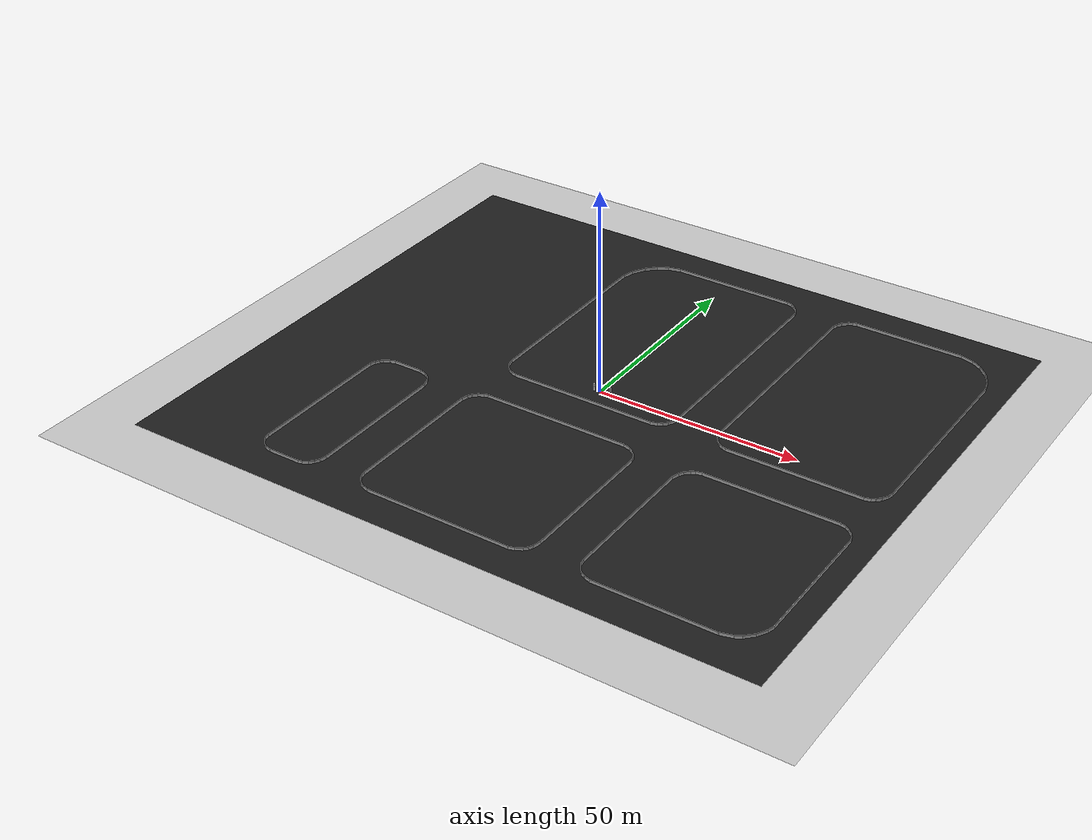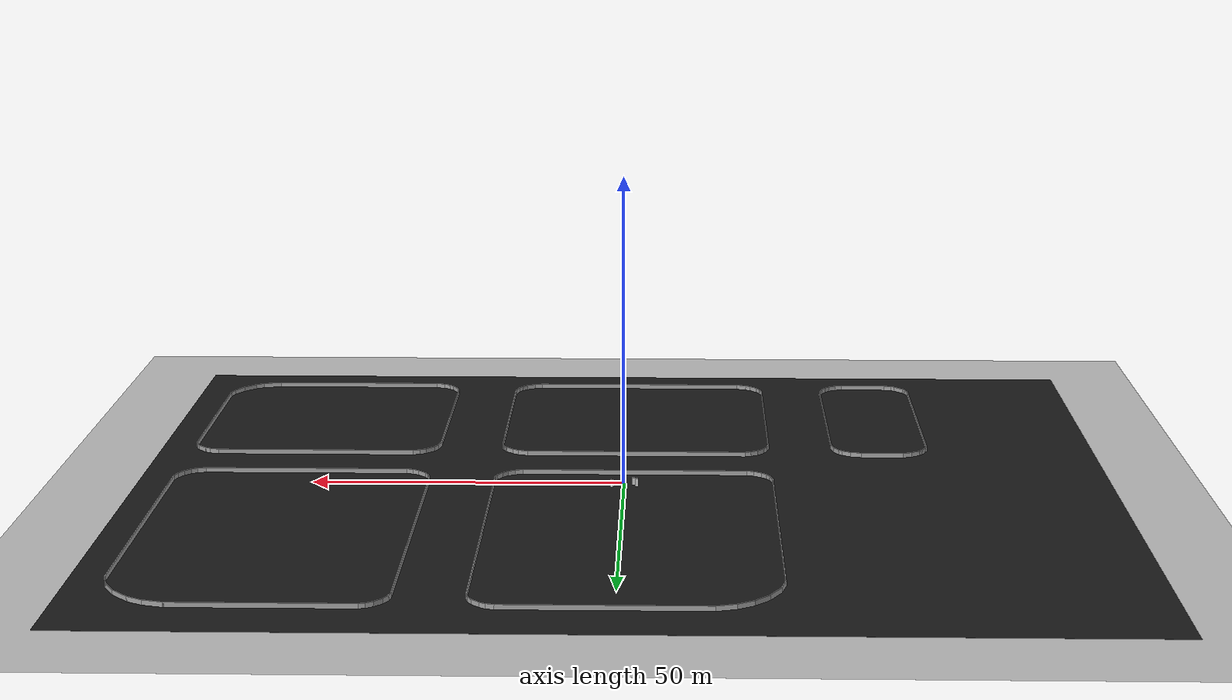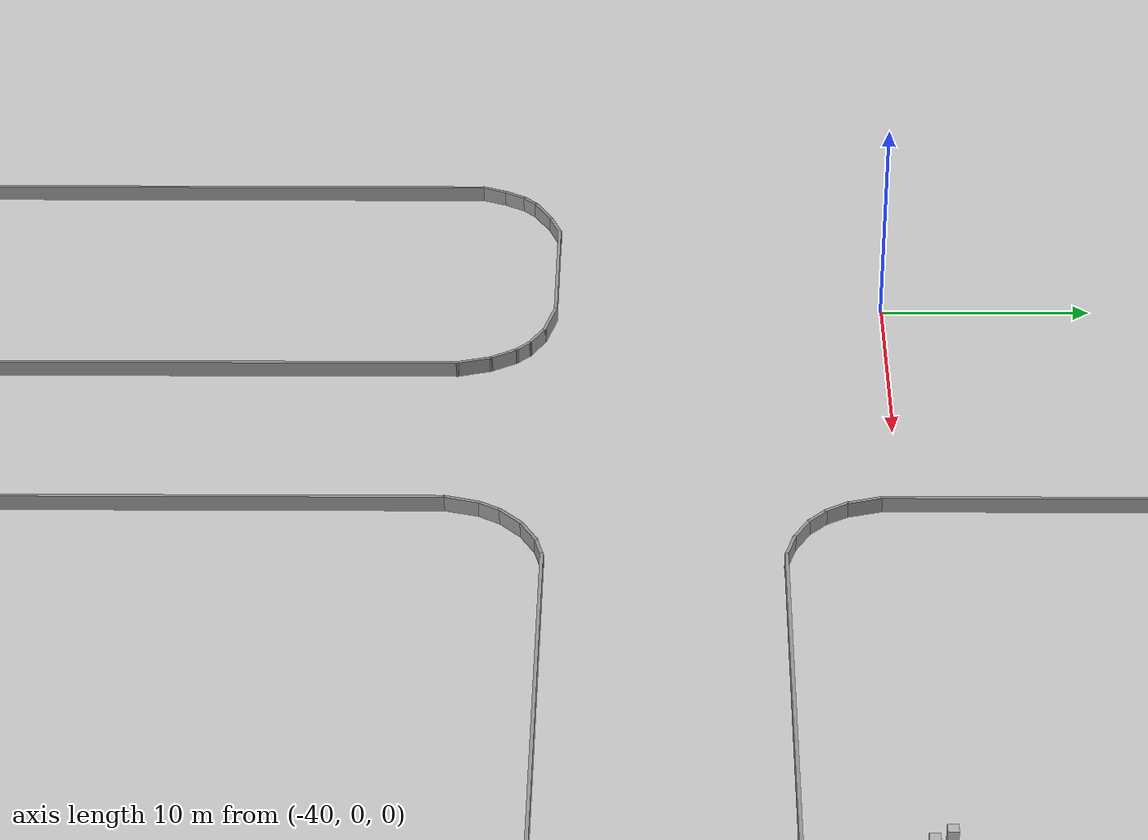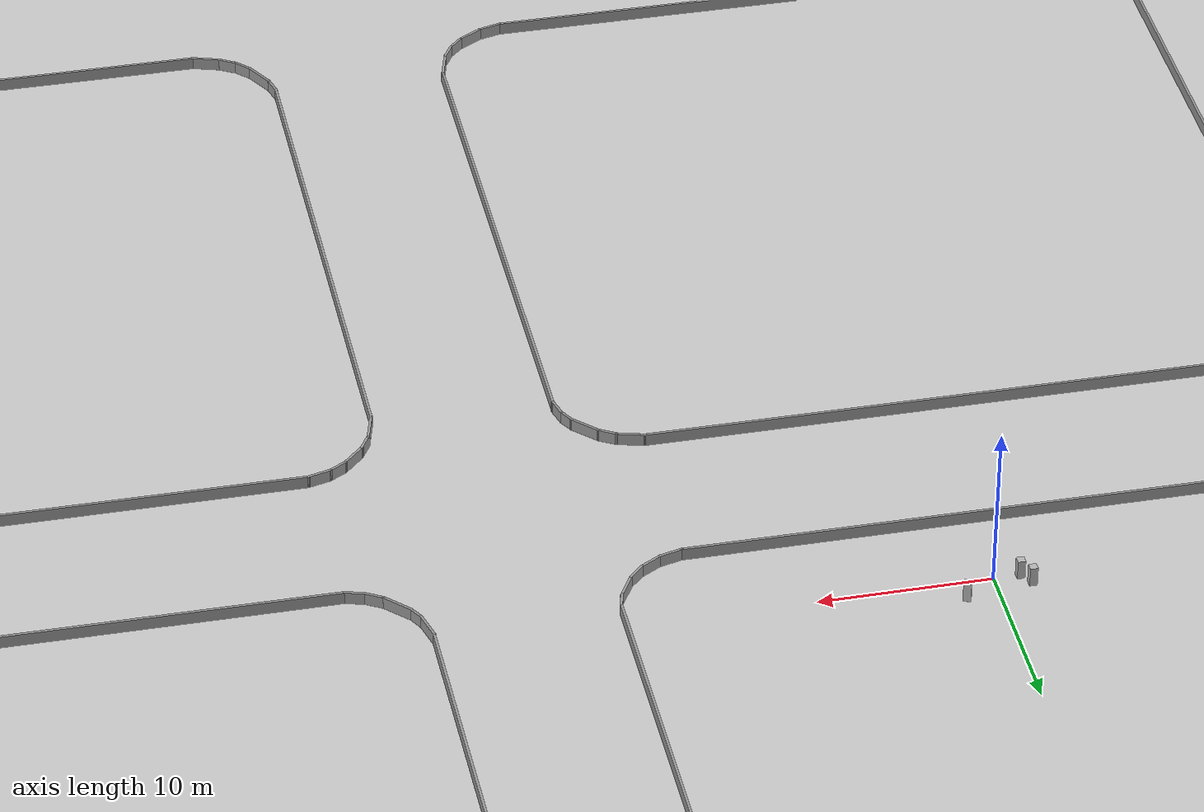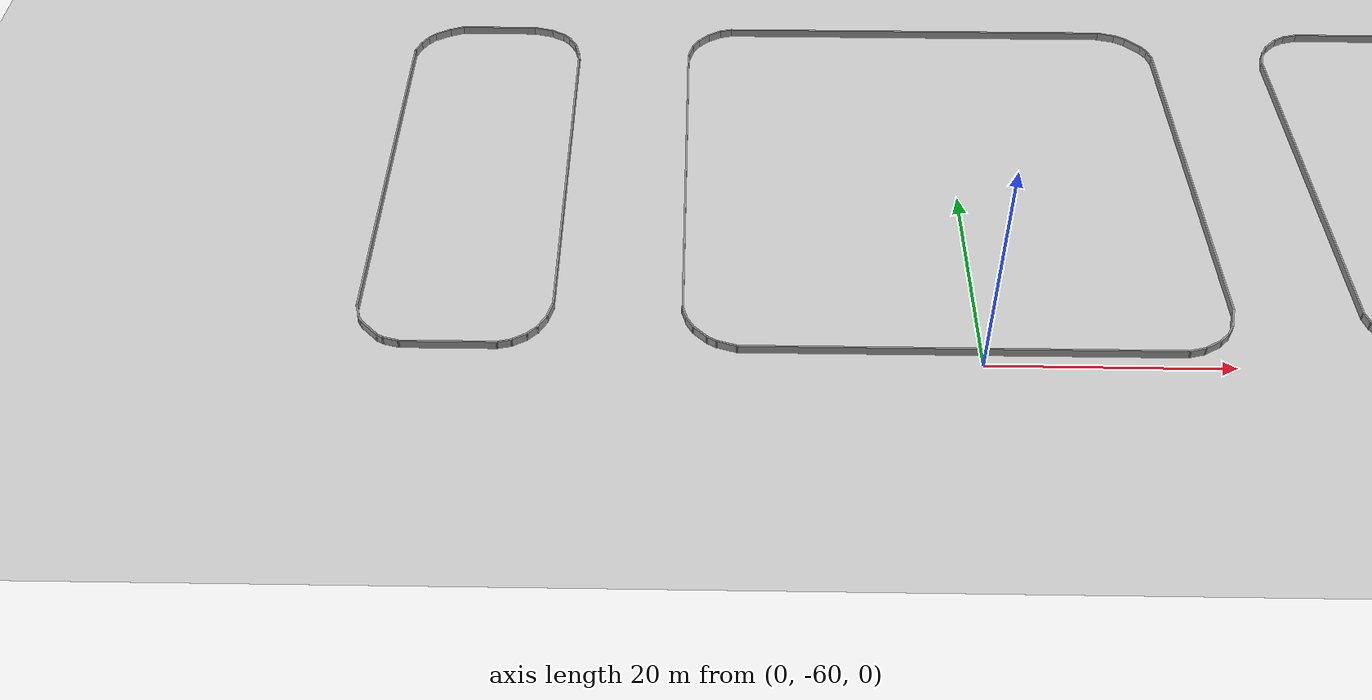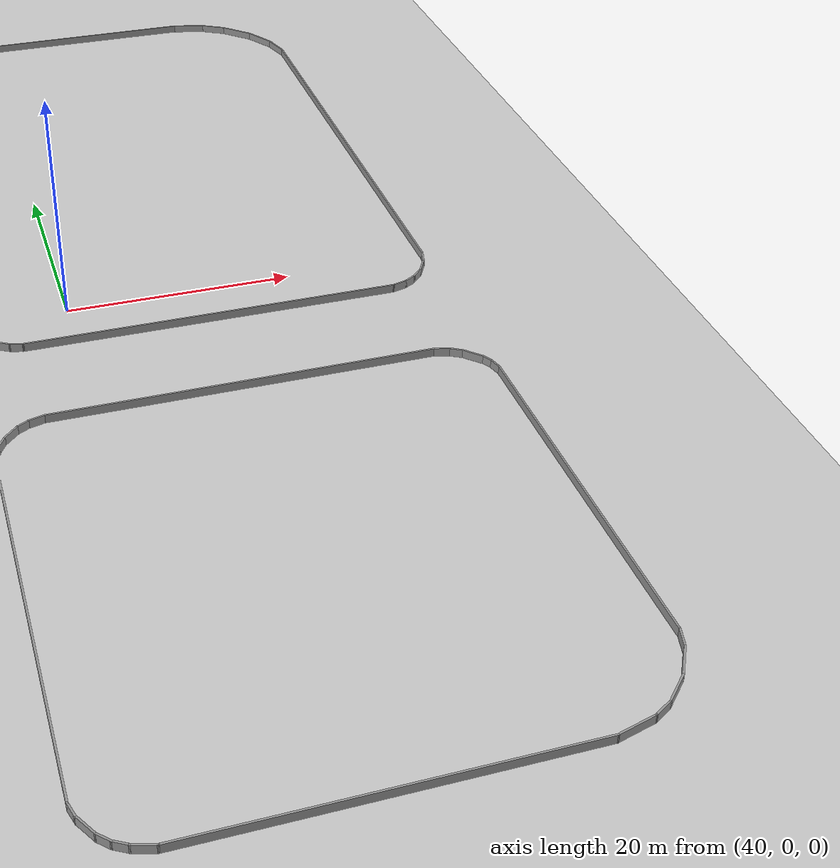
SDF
<sdf version="1.6">
 <world name="default">
  <scene>
   <ambient>0 0 0 1</ambient>
   <shadows>0</shadows>
   <grid>0</grid>
   <background>0.7 0.7 0.7 1</background>
  </scene>
  <include><uri>model://isaretler/dur</uri><pose>1.84 1.27 0.13 0 0 -0.356</pose></include>
  <include><uri>model://isaretler/durak</uri><pose>-1.544 -0.08 0.125 0 0 0</pose></include>
  <include><uri>model://isaretler/giris_olmayan_yol</uri><pose>-2.05 0.65 0.125 0 -0 0</pose></include>
  <include><uri>model://isaretler/park_etmek_yasaktir</uri><pose>-2.05 0.65 0.125 0 -0 0</pose></include>
  <include><uri>model://isaretler/park_yeri</uri><pose>-2.05 0.65 0.125 0 -0 0</pose></include>
  <include><uri>model://map</uri></include>
  <include><uri>model://ic_bariyerler</uri></include>
  <light name="sun" type="directional">
   <pose>0 0 10 0 -0 0</pose>
   <diffuse>0.8 0.8 0.8 1</diffuse>
   <specular>0.1 0.1 0.1 1</specular>
   <attenuation>
    <range>1000</range>
    <constant>0.9</constant>
    <linear>0.01</linear>
    <quadratic>0.001</quadratic>
   </attenuation>
   <direction>-0.5 0.5 -1</direction>
  </light>
  <model name="ground2">
   <pose>0 0 -0.1 0 -0 0</pose>
   <static>1</static>
   <link name="ground">
    <collision name="ground_coll"><geometry><box><size>156.72 133.83 0.01</size></box></geometry></collision>
    <visual name="ground_vis">
     <geometry><box><size>156.72 133.83 0.01</size></box></geometry>
     <material>
      <script><uri>file://media/materials/scripts/gazebo.material</uri><name>Gazebo/FlatBlack</name></script>
     </material>
    </visual>
   </link>
  </model>
  <gravity>0 0 -9.8</gravity>
  <magnetic_field>6e-06 2.3e-05 -4.2e-05</magnetic_field>
  <atmosphere type="adiabatic"/>
  <physics name="default_physics" default="0" type="ode">
   <max_step_size>0.001</max_step_size>
   <real_time_factor>1</real_time_factor>
   <real_time_update_rate>1000</real_time_update_rate>
  </physics>
  <spherical_coordinates>
   <surface_model>EARTH_WGS84</surface_model>
   <latitude_deg>0</latitude_deg>
   <longitude_deg>0</longitude_deg>
   <elevation>0</elevation>
   <heading_deg>0</heading_deg>
  </spherical_coordinates>
  <light name="user_point_light_2" type="point">
   <pose>-0.948146 0.604519 1 0 -0 0</pose>
   <diffuse>0.5 0.5 0.5 1</diffuse>
   <specular>0.1 0.1 0.1 1</specular>
   <attenuation>
    <range>20</range>
    <constant>0.5</constant>
    <linear>0.01</linear>
    <quadratic>0.001</quadratic>
   </attenuation>
   <cast_shadows>0</cast_shadows>
   <direction>0 0 -1</direction>
  </light>
  <light name="user_point_light_6" type="point">
   <pose>1.63854 1.69565 1 0 -0 0</pose>
   <diffuse>0.5 0.5 0.5 1</diffuse>
   <specular>0.1 0.1 0.1 1</specular>
   <attenuation>
    <range>20</range>
    <constant>0.5</constant>
    <linear>0.01</linear>
    <quadratic>0.001</quadratic>
   </attenuation>
   <cast_shadows>0</cast_shadows>
   <direction>0 0 -1</direction>
  </light>
  <light name="user_point_light_7" type="point">
   <pose>0.42  -3.31 1 0 -0 0</pose>
   <diffuse>0.5 0.5 0.5 1</diffuse>
   <specular>0.1 0.1 0.1 1</specular>
   <attenuation>
    <range>20</range>
    <constant>0.5</constant>
    <linear>0.01</linear>
    <quadratic>0.001</quadratic>
   </attenuation>
   <cast_shadows>0</cast_shadows>
   <direction>0 0 -1</direction>
  </light>
  <light name="user_point_light_8" type="point">
   <pose>-1.8 1.5 1 0 -0 0</pose>
   <diffuse>0.5 0.5 0.5 1</diffuse>
   <specular>0.1 0.1 0.1 1</specular>
   <attenuation>
    <range>20</range>
    <constant>0.5</constant>
    <linear>0.01</linear>
    <quadratic>0.001</quadratic>
   </attenuation>
   <cast_shadows>0</cast_shadows>
   <direction>0 0 -1</direction>
  </light>
 </world>
</sdf>

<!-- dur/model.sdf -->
<sdf version="1.6">
  <model name="dur">
    <static>true</static>
    <link name="box">
      <pose>0 0 0 0 0 0</pose>
      <collision name="collision">
        <geometry>
          <box>
            <size>0.45 0.45 2</size>
          </box>
        </geometry>
      </collision>
      <visual name="visual">
        <geometry>
          <box>
            <size>0.45 0.45 2</size>
          </box>
        </geometry>
        <material>
          <script>
            <uri>model://turtlebot3_autorace/dur/materials/scripts</uri>
            <uri>model://turtlebot3_autorace/dur/materials/textures</uri>
            <name>dur</name>
          </script>
        </material>
      </visual>
    </link>
  </model>
</sdf>

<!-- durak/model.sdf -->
<sdf version="1.6">
  <model name="isaret_durak">
    <static>true</static>
    <link name="box">
      <pose>0 0 0 0 0 0</pose>
      <collision name="collision">
        <geometry>
          <box>
            <size>0.45 0.45 2</size>
          </box>
        </geometry>
      </collision>
      <visual name="visual">
        <geometry>
          <box>
            <size>0.45 0.45 2</size>
          </box>
        </geometry>
        <material>
          <script>
            <uri>model://turtlebot3_autorace/durak/materials/scripts</uri>
            <uri>model://turtlebot3_autorace/durak/materials/textures</uri>
            <name>isaret_durak</name>
          </script>
        </material>
      </visual>
    </link>
  </model>
</sdf>

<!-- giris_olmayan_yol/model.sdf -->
<sdf version="1.6">
  <model name="isaret_giris_olmayan_yol">
    <static>true</static>
    <link name="box">
      <pose>0 0 0 0 0 0</pose>
      <collision name="collision">
        <geometry>
          <box>
            <size>0.45 0.45 2</size>
          </box>
        </geometry>
      </collision>
      <visual name="visual">
        <geometry>
          <box>
            <size>0.45 0.45 2</size>
          </box>
        </geometry>
        <material>
          <script>
            <uri>model://turtlebot3_autorace/giris_olmayan_yol/materials/scripts</uri>
            <uri>model://turtlebot3_autorace/giris_olmayan_yol/materials/textures</uri>
            <name>isaret_giris_olmayan_yol</name>
          </script>
        </material>
      </visual>
    </link>
  </model>
</sdf>

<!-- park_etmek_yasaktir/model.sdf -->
<sdf version="1.6">
  <model name="isaret_park_etmek_yasaktir">
    <static>true</static>
    <link name="box">
      <pose>0 0 0 0 0 0</pose>
      <collision name="collision">
        <geometry>
          <box>
            <size>0.45 0.45 2</size>
          </box>
        </geometry>
      </collision>
      <visual name="visual">
        <geometry>
          <box>
            <size>0.45 0.45 2</size>
          </box>
        </geometry>
        <material>
          <script>
            <uri>model://turtlebot3_autorace/park_etmek_yasaktir/materials/scripts</uri>
            <uri>model://turtlebot3_autorace/park_etmek_yasaktir/materials/textures</uri>
            <name>isaret_park_etmek_yasaktir</name>
          </script>
        </material>
      </visual>
    </link>
  </model>
</sdf>

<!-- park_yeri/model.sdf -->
<sdf version="1.6">
  <model name="isaret_park_yeri">
    <static>true</static>
    <link name="box">
      <pose>0 0 0 0 0 0</pose>
      <collision name="collision">
        <geometry>
          <box>
            <size>0.45 0.45 2</size>
          </box>
        </geometry>
      </collision>
      <visual name="visual">
        <geometry>
          <box>
            <size>0.45 0.45 2</size>
          </box>
        </geometry>
        <material>
          <script>
            <uri>model://turtlebot3_autorace/park_yeri/materials/scripts</uri>
            <uri>model://turtlebot3_autorace/park_yeri/materials/textures</uri>
            <name>isaret_park_yeri</name>
          </script>
        </material>
      </visual>
    </link>
  </model>
</sdf>

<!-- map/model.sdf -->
<sdf version="1.6">
  <model name="course">
    <static>true</static>
    <link name="course_link">
      <collision name="course_collision">
        <geometry>
          <plane>
            <normal>0 0 1</normal>
            <size>150 100</size>
          </plane>
        </geometry>
        <surface>
          <friction>
            <ode>
              <mu>100</mu>
              <mu2>50</mu2>
            </ode>
          </friction>
        </surface>
      </collision>
      <visual name="course_visual">
        <cast_shadows>false</cast_shadows>
        <geometry>
	        <plane>
            <normal>0 0 1</normal>
            <size>150 100</size>
          </plane>
        </geometry>
	      <material>
          <script>
            <uri>model://turtlebot3_autorace/course/materials/scripts</uri>
            <uri>model://turtlebot3_autorace/course/materials/textures</uri>
            <name>course</name>
          </script>
        </material>
      </visual>
    </link>
  </model>
</sdf>

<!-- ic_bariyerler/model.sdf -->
<sdf version='1.6'>
  <model name='Ic_Duvarlar'>
    <pose frame=''>11.1232 -0.483385 0 0 -0 0</pose>
    <link name='Wall_0'>
      <collision name='Wall_0_Collision'>
        <geometry>
          <box>
            <size>35.25 0.15 0.75</size>
          </box>
        </geometry>
        <pose frame=''>0 0 0.375 0 -0 0</pose>
      </collision>
      <visual name='Wall_0_Visual'>
        <pose frame=''>0 0 0.375 0 -0 0</pose>
        <geometry>
          <box>
            <size>35.25 0.15 0.75</size>
          </box>
        </geometry>
        <material>
          <script>
            <uri>file://media/materials/scripts/gazebo.material</uri>
            <name>Gazebo/Grey</name>
          </script>
          <ambient>1 1 1 1</ambient>
        </material>
      </visual>
      <pose frame=''>-61.5911 -36.6736 0 0 0 -1.5708</pose>
    </link>
    <link name='Wall_1'>
      <collision name='Wall_1_Collision'>
        <geometry>
          <box>
            <size>1.5 0.15 0.75</size>
          </box>
        </geometry>
        <pose frame=''>0 0 0.375 0 -0 0</pose>
      </collision>
      <visual name='Wall_1_Visual'>
        <pose frame=''>0 0 0.375 0 -0 0</pose>
        <geometry>
          <box>
            <size>1.5 0.15 0.75</size>
          </box>
        </geometry>
        <material>
          <script>
            <uri>file://media/materials/scripts/gazebo.material</uri>
            <name>Gazebo/Grey</name>
          </script>
          <ambient>1 1 1 1</ambient>
        </material>
      </visual>
      <pose frame=''>-61.4162 -54.8756 0 0 0 -1.30857</pose>
    </link>
    <link name='Wall_101'>
      <collision name='Wall_101_Collision'>
        <geometry>
          <box>
            <size>1.5 0.15 0.75</size>
          </box>
        </geometry>
        <pose frame=''>0 0 0.375 0 -0 0</pose>
      </collision>
      <visual name='Wall_101_Visual'>
        <pose frame=''>0 0 0.375 0 -0 0</pose>
        <geometry>
          <box>
            <size>1.5 0.15 0.75</size>
          </box>
        </geometry>
        <material>
          <script>
            <uri>file://media/materials/scripts/gazebo.material</uri>
            <name>Gazebo/Grey</name>
          </script>
          <ambient>1 1 1 1</ambient>
        </material>
      </visual>
      <pose frame=''>6.14385 58.0924 0 0 -0 2.87937</pose>
    </link>
    <link name='Wall_102'>
      <collision name='Wall_102_Collision'>
        <geometry>
          <box>
            <size>30.5 0.15 0.75</size>
          </box>
        </geometry>
        <pose frame=''>0 0 0.375 0 -0 0</pose>
      </collision>
      <visual name='Wall_102_Visual'>
        <pose frame=''>0 0 0.375 0 -0 0</pose>
        <geometry>
          <box>
            <size>30.5 0.15 0.75</size>
          </box>
        </geometry>
        <material>
          <script>
            <uri>file://media/materials/scripts/gazebo.material</uri>
            <name>Gazebo/Grey</name>
          </script>
          <ambient>1 1 1 1</ambient>
        </material>
      </visual>
      <pose frame=''>-9.68315 58.2674 0 0 -0 3.14159</pose>
    </link>
    <link name='Wall_107'>
      <collision name='Wall_107_Collision'>
        <geometry>
          <box>
            <size>3.25 0.15 0.75</size>
          </box>
        </geometry>
        <pose frame=''>0 0 0.375 0 -0 0</pose>
      </collision>
      <visual name='Wall_107_Visual'>
        <pose frame=''>0 0 0.375 0 -0 0</pose>
        <geometry>
          <box>
            <size>3.25 0.15 0.75</size>
          </box>
        </geometry>
        <material>
          <script>
            <uri>file://media/materials/scripts/gazebo.material</uri>
            <name>Gazebo/Grey</name>
          </script>
          <ambient>1 1 1 1</ambient>
        </material>
      </visual>
      <pose frame=''>-26.3557 57.8659 0 0 0 -2.87964</pose>
    </link>
    <link name='Wall_108'>
      <collision name='Wall_108_Collision'>
        <geometry>
          <box>
            <size>3 0.15 0.75</size>
          </box>
        </geometry>
        <pose frame=''>0 0 0.375 0 -0 0</pose>
      </collision>
      <visual name='Wall_108_Visual'>
        <pose frame=''>0 0 0.375 0 -0 0</pose>
        <geometry>
          <box>
            <size>3 0.15 0.75</size>
          </box>
        </geometry>
        <material>
          <script>
            <uri>file://media/materials/scripts/gazebo.material</uri>
            <name>Gazebo/Grey</name>
          </script>
          <ambient>1 1 1 1</ambient>
        </material>
      </visual>
      <pose frame=''>-29.0872 56.7519 0 0 0 -2.61796</pose>
    </link>
    <link name='Wall_110'>
      <collision name='Wall_110_Collision'>
        <geometry>
          <box>
            <size>3.25 0.15 0.75</size>
          </box>
        </geometry>
        <pose frame=''>0 0 0.375 0 -0 0</pose>
      </collision>
      <visual name='Wall_110_Visual'>
        <pose frame=''>0 0 0.375 0 -0 0</pose>
        <geometry>
          <box>
            <size>3.25 0.15 0.75</size>
          </box>
        </geometry>
        <material>
          <script>
            <uri>file://media/materials/scripts/gazebo.material</uri>
            <name>Gazebo/Grey</name>
          </script>
          <ambient>1 1 1 1</ambient>
        </material>
      </visual>
      <pose frame=''>-31.4172 54.9434 0 0 0 -2.35619</pose>
    </link>
    <link name='Wall_111'>
      <collision name='Wall_111_Collision'>
        <geometry>
          <box>
            <size>3.75 0.15 0.75</size>
          </box>
        </geometry>
        <pose frame=''>0 0 0.375 0 -0 0</pose>
      </collision>
      <visual name='Wall_111_Visual'>
        <pose frame=''>0 0 0.375 0 -0 0</pose>
        <geometry>
          <box>
            <size>3.75 0.15 0.75</size>
          </box>
        </geometry>
        <material>
          <script>
            <uri>file://media/materials/scripts/gazebo.material</uri>
            <name>Gazebo/Grey</name>
          </script>
          <ambient>1 1 1 1</ambient>
        </material>
      </visual>
      <pose frame=''>-33.4132 52.2889 0 0 0 -2.09449</pose>
    </link>
    <link name='Wall_113'>
      <collision name='Wall_113_Collision'>
        <geometry>
          <box>
            <size>3 0.15 0.75</size>
          </box>
        </geometry>
        <pose frame=''>0 0 0.375 0 -0 0</pose>
      </collision>
      <visual name='Wall_113_Visual'>
        <pose frame=''>0 0 0.375 0 -0 0</pose>
        <geometry>
          <box>
            <size>3 0.15 0.75</size>
          </box>
        </geometry>
        <material>
          <script>
            <uri>file://media/materials/scripts/gazebo.material</uri>
            <name>Gazebo/Grey</name>
          </script>
          <ambient>1 1 1 1</ambient>
        </material>
      </visual>
      <pose frame=''>-34.6817 49.3539 0 0 0 -1.83237</pose>
    </link>
    <link name='Wall_115'>
      <collision name='Wall_115_Collision'>
        <geometry>
          <box>
            <size>48.5 0.15 0.75</size>
          </box>
        </geometry>
        <pose frame=''>0 0 0.375 0 -0 0</pose>
      </collision>
      <visual name='Wall_115_Visual'>
        <pose frame=''>0 0 0.375 0 -0 0</pose>
        <geometry>
          <box>
            <size>48.5 0.15 0.75</size>
          </box>
        </geometry>
        <material>
          <script>
            <uri>file://media/materials/scripts/gazebo.material</uri>
            <name>Gazebo/Grey</name>
          </script>
          <ambient>1 1 1 1</ambient>
        </material>
      </visual>
      <pose frame=''>-35.0502 23.8024 0 0 0 -1.5708</pose>
    </link>
    <link name='Wall_116'>
      <collision name='Wall_116_Collision'>
        <geometry>
          <box>
            <size>1.75 0.15 0.75</size>
          </box>
        </geometry>
        <pose frame=''>0 0 0.375 0 -0 0</pose>
      </collision>
      <visual name='Wall_116_Visual'>
        <pose frame=''>0 0 0.375 0 -0 0</pose>
        <geometry>
          <box>
            <size>1.75 0.15 0.75</size>
          </box>
        </geometry>
        <material>
          <script>
            <uri>file://media/materials/scripts/gazebo.material</uri>
            <name>Gazebo/Grey</name>
          </script>
          <ambient>1 1 1 1</ambient>
        </material>
      </visual>
      <pose frame=''>-34.8432 -1.14562 0 0 0 -1.30915</pose>
    </link>
    <link name='Wall_117'>
      <collision name='Wall_117_Collision'>
        <geometry>
          <box>
            <size>1.25 0.15 0.75</size>
          </box>
        </geometry>
        <pose frame=''>0 0 0.375 0 -0 0</pose>
      </collision>
      <visual name='Wall_117_Visual'>
        <pose frame=''>0 0 0.375 0 -0 0</pose>
        <geometry>
          <box>
            <size>1.25 0.15 0.75</size>
          </box>
        </geometry>
        <material>
          <script>
            <uri>file://media/materials/scripts/gazebo.material</uri>
            <name>Gazebo/Grey</name>
          </script>
          <ambient>1 1 1 1</ambient>
        </material>
      </visual>
      <pose frame=''>-34.3612 -2.39461 0 0 0 -1.04691</pose>
    </link>
    <link name='Wall_118'>
      <collision name='Wall_118_Collision'>
        <geometry>
          <box>
            <size>1.25 0.15 0.75</size>
          </box>
        </geometry>
        <pose frame=''>0 0 0.375 0 -0 0</pose>
      </collision>
      <visual name='Wall_118_Visual'>
        <pose frame=''>0 0 0.375 0 -0 0</pose>
        <geometry>
          <box>
            <size>1.25 0.15 0.75</size>
          </box>
        </geometry>
        <material>
          <script>
            <uri>file://media/materials/scripts/gazebo.material</uri>
            <name>Gazebo/Grey</name>
          </script>
          <ambient>1 1 1 1</ambient>
        </material>
      </visual>
      <pose frame=''>-33.6972 -3.25962 0 0 0 -0.785398</pose>
    </link>
    <link name='Wall_120'>
      <collision name='Wall_120_Collision'>
        <geometry>
          <box>
            <size>1.39796 0.15 0.75</size>
          </box>
        </geometry>
        <pose frame=''>0 0 0.375 0 -0 0</pose>
      </collision>
      <visual name='Wall_120_Visual'>
        <pose frame=''>0 0 0.375 0 -0 0</pose>
        <geometry>
          <box>
            <size>1.39796 0.15 0.75</size>
          </box>
        </geometry>
        <material>
          <script>
            <uri>file://media/materials/scripts/gazebo.material</uri>
            <name>Gazebo/Grey</name>
          </script>
          <ambient>1 1 1 1</ambient>
        </material>
      </visual>
      <pose frame=''>-31.5427 -4.50662 0 0 0 -0.297674</pose>
    </link>
    <link name='Wall_122'>
      <collision name='Wall_122_Collision'>
        <geometry>
          <box>
            <size>33 0.15 0.75</size>
          </box>
        </geometry>
        <pose frame=''>0 0 0.375 0 -0 0</pose>
      </collision>
      <visual name='Wall_122_Visual'>
        <pose frame=''>0 0 0.375 0 -0 0</pose>
        <geometry>
          <box>
            <size>33 0.15 0.75</size>
          </box>
        </geometry>
        <material>
          <script>
            <uri>file://media/materials/scripts/gazebo.material</uri>
            <name>Gazebo/Grey</name>
          </script>
          <ambient>1 1 1 1</ambient>
        </material>
      </visual>
      <pose frame=''>40.8108 -4.68461 0 0 -0 0</pose>
    </link>
    <link name='Wall_123'>
      <collision name='Wall_123_Collision'>
        <geometry>
          <box>
            <size>1.5 0.15 0.75</size>
          </box>
        </geometry>
        <pose frame=''>0 0 0.375 0 -0 0</pose>
      </collision>
      <visual name='Wall_123_Visual'>
        <pose frame=''>0 0 0.375 0 -0 0</pose>
        <geometry>
          <box>
            <size>1.5 0.15 0.75</size>
          </box>
        </geometry>
        <material>
          <script>
            <uri>file://media/materials/scripts/gazebo.material</uri>
            <name>Gazebo/Grey</name>
          </script>
          <ambient>1 1 1 1</ambient>
        </material>
      </visual>
      <pose frame=''>57.8879 -4.51011 0 0 -0 0.261509</pose>
    </link>
    <link name='Wall_124'>
      <collision name='Wall_124_Collision'>
        <geometry>
          <box>
            <size>1.25 0.15 0.75</size>
          </box>
        </geometry>
        <pose frame=''>0 0 0.375 0 -0 0</pose>
      </collision>
      <visual name='Wall_124_Visual'>
        <pose frame=''>0 0 0.375 0 -0 0</pose>
        <geometry>
          <box>
            <size>1.25 0.15 0.75</size>
          </box>
        </geometry>
        <material>
          <script>
            <uri>file://media/materials/scripts/gazebo.material</uri>
            <name>Gazebo/Grey</name>
          </script>
          <ambient>1 1 1 1</ambient>
        </material>
      </visual>
      <pose frame=''>59.0164 -4.06062 0 0 -0 0.52343</pose>
    </link>
    <link name='Wall_125'>
      <collision name='Wall_125_Collision'>
        <geometry>
          <box>
            <size>1.5 0.15 0.75</size>
          </box>
        </geometry>
        <pose frame=''>0 0 0.375 0 -0 0</pose>
      </collision>
      <visual name='Wall_125_Visual'>
        <pose frame=''>0 0 0.375 0 -0 0</pose>
        <geometry>
          <box>
            <size>1.5 0.15 0.75</size>
          </box>
        </geometry>
        <material>
          <script>
            <uri>file://media/materials/scripts/gazebo.material</uri>
            <name>Gazebo/Grey</name>
          </script>
          <ambient>1 1 1 1</ambient>
        </material>
      </visual>
      <pose frame=''>59.9703 -3.30811 0 0 -0 0.785398</pose>
    </link>
    <link name='Wall_126'>
      <collision name='Wall_126_Collision'>
        <geometry>
          <box>
            <size>1.75 0.15 0.75</size>
          </box>
        </geometry>
        <pose frame=''>0 0 0.375 0 -0 0</pose>
      </collision>
      <visual name='Wall_126_Visual'>
        <pose frame=''>0 0 0.375 0 -0 0</pose>
        <geometry>
          <box>
            <size>1.75 0.15 0.75</size>
          </box>
        </geometry>
        <material>
          <script>
            <uri>file://media/materials/scripts/gazebo.material</uri>
            <name>Gazebo/Grey</name>
          </script>
          <ambient>1 1 1 1</ambient>
        </material>
      </visual>
      <pose frame=''>60.8478 -2.13811 0 0 -0 1.047</pose>
    </link>
    <link name='Wall_130'>
      <collision name='Wall_130_Collision'>
        <geometry>
          <box>
            <size>1.5 0.15 0.75</size>
          </box>
        </geometry>
        <pose frame=''>0 0 0.375 0 -0 0</pose>
      </collision>
      <visual name='Wall_130_Visual'>
        <pose frame=''>0 0 0.375 0 -0 0</pose>
        <geometry>
          <box>
            <size>1.5 0.15 0.75</size>
          </box>
        </geometry>
        <material>
          <script>
            <uri>file://media/materials/scripts/gazebo.material</uri>
            <name>Gazebo/Grey</name>
          </script>
          <ambient>1 1 1 1</ambient>
        </material>
      </visual>
      <pose frame=''>61.4224 -0.793615 0 0 -0 1.30929</pose>
    </link>
    <link name='Wall_131'>
      <collision name='Wall_131_Collision'>
        <geometry>
          <box>
            <size>48.25 0.15 0.75</size>
          </box>
        </geometry>
        <pose frame=''>0 0 0.375 0 -0 0</pose>
      </collision>
      <visual name='Wall_131_Visual'>
        <pose frame=''>0 0 0.375 0 -0 0</pose>
        <geometry>
          <box>
            <size>48.25 0.15 0.75</size>
          </box>
        </geometry>
        <material>
          <script>
            <uri>file://media/materials/scripts/gazebo.material</uri>
            <name>Gazebo/Grey</name>
          </script>
          <ambient>1 1 1 1</ambient>
        </material>
      </visual>
      <pose frame=''>61.5968 23.9084 0 0 -0 1.5708</pose>
    </link>
    <link name='Wall_132'>
      <collision name='Wall_132_Collision'>
        <geometry>
          <box>
            <size>3 0.15 0.75</size>
          </box>
        </geometry>
        <pose frame=''>0 0 0.375 0 -0 0</pose>
      </collision>
      <visual name='Wall_132_Visual'>
        <pose frame=''>0 0 0.375 0 -0 0</pose>
        <geometry>
          <box>
            <size>3 0.15 0.75</size>
          </box>
        </geometry>
        <material>
          <script>
            <uri>file://media/materials/scripts/gazebo.material</uri>
            <name>Gazebo/Grey</name>
          </script>
          <ambient>1 1 1 1</ambient>
        </material>
      </visual>
      <pose frame=''>61.2278 49.3349 0 0 -0 1.83271</pose>
    </link>
    <link name='Wall_133'>
      <collision name='Wall_133_Collision'>
        <geometry>
          <box>
            <size>3.5 0.15 0.75</size>
          </box>
        </geometry>
        <pose frame=''>0 0 0.375 0 -0 0</pose>
      </collision>
      <visual name='Wall_133_Visual'>
        <pose frame=''>0 0 0.375 0 -0 0</pose>
        <geometry>
          <box>
            <size>3.5 0.15 0.75</size>
          </box>
        </geometry>
        <material>
          <script>
            <uri>file://media/materials/scripts/gazebo.material</uri>
            <name>Gazebo/Grey</name>
          </script>
          <ambient>1 1 1 1</ambient>
        </material>
      </visual>
      <pose frame=''>60.0213 52.1624 0 0 -0 2.09427</pose>
    </link>
    <link name='Wall_134'>
      <collision name='Wall_134_Collision'>
        <geometry>
          <box>
            <size>3.75 0.15 0.75</size>
          </box>
        </geometry>
        <pose frame=''>0 0 0.375 0 -0 0</pose>
      </collision>
      <visual name='Wall_134_Visual'>
        <pose frame=''>0 0 0.375 0 -0 0</pose>
        <geometry>
          <box>
            <size>3.75 0.15 0.75</size>
          </box>
        </geometry>
        <material>
          <script>
            <uri>file://media/materials/scripts/gazebo.material</uri>
            <name>Gazebo/Grey</name>
          </script>
          <ambient>1 1 1 1</ambient>
        </material>
      </visual>
      <pose frame=''>57.9113 54.8859 0 0 -0 2.35619</pose>
    </link>
    <link name='Wall_135'>
      <collision name='Wall_135_Collision'>
        <geometry>
          <box>
            <size>2.75 0.15 0.75</size>
          </box>
        </geometry>
        <pose frame=''>0 0 0.375 0 -0 0</pose>
      </collision>
      <visual name='Wall_135_Visual'>
        <pose frame=''>0 0 0.375 0 -0 0</pose>
        <geometry>
          <box>
            <size>2.75 0.15 0.75</size>
          </box>
        </geometry>
        <material>
          <script>
            <uri>file://media/materials/scripts/gazebo.material</uri>
            <name>Gazebo/Grey</name>
          </script>
          <ambient>1 1 1 1</ambient>
        </material>
      </visual>
      <pose frame=''>55.5129 56.8084 0 0 -0 2.61806</pose>
    </link>
    <link name='Wall_136'>
      <collision name='Wall_136_Collision'>
        <geometry>
          <box>
            <size>3.5 0.15 0.75</size>
          </box>
        </geometry>
        <pose frame=''>0 0 0.375 0 -0 0</pose>
      </collision>
      <visual name='Wall_136_Visual'>
        <pose frame=''>0 0 0.375 0 -0 0</pose>
        <geometry>
          <box>
            <size>3.5 0.15 0.75</size>
          </box>
        </geometry>
        <material>
          <script>
            <uri>file://media/materials/scripts/gazebo.material</uri>
            <name>Gazebo/Grey</name>
          </script>
          <ambient>1 1 1 1</ambient>
        </material>
      </visual>
      <pose frame=''>52.7688 57.8919 0 0 -0 2.87982</pose>
    </link>
    <link name='Wall_137'>
      <collision name='Wall_137_Collision'>
        <geometry>
          <box>
            <size>27.01 0.15 0.75</size>
          </box>
        </geometry>
        <pose frame=''>0 0 0.375 0 -0 0</pose>
      </collision>
      <visual name='Wall_137_Visual'>
        <pose frame=''>0 0 0.375 0 -0 0</pose>
        <geometry>
          <box>
            <size>27.01 0.15 0.75</size>
          </box>
        </geometry>
        <material>
          <script>
            <uri>file://media/materials/scripts/gazebo.material</uri>
            <name>Gazebo/Grey</name>
          </script>
          <ambient>1 1 1 1</ambient>
        </material>
      </visual>
      <pose frame=''>37.7208 58.3254 0 0 -0 3.14159</pose>
    </link>
    <link name='Wall_138'>
      <collision name='Wall_138_Collision'>
        <geometry>
          <box>
            <size>1.24002 0.15 0.75</size>
          </box>
        </geometry>
        <pose frame=''>0 0 0.375 0 -0 0</pose>
      </collision>
      <visual name='Wall_138_Visual'>
        <pose frame=''>0 0 0.375 0 -0 0</pose>
        <geometry>
          <box>
            <size>1.24002 0.15 0.75</size>
          </box>
        </geometry>
        <material>
          <script>
            <uri>file://media/materials/scripts/gazebo.material</uri>
            <name>Gazebo/Grey</name>
          </script>
          <ambient>1 1 1 1</ambient>
        </material>
      </visual>
      <pose frame=''>23.7648 58.1829 0 0 0 -2.87703</pose>
    </link>
    <link name='Wall_139'>
      <collision name='Wall_139_Collision'>
        <geometry>
          <box>
            <size>1.25 0.15 0.75</size>
          </box>
        </geometry>
        <pose frame=''>0 0 0.375 0 -0 0</pose>
      </collision>
      <visual name='Wall_139_Visual'>
        <pose frame=''>0 0 0.375 0 -0 0</pose>
        <geometry>
          <box>
            <size>1.25 0.15 0.75</size>
          </box>
        </geometry>
        <material>
          <script>
            <uri>file://media/materials/scripts/gazebo.material</uri>
            <name>Gazebo/Grey</name>
          </script>
          <ambient>1 1 1 1</ambient>
        </material>
      </visual>
      <pose frame=''>22.7624 57.7654 0 0 0 -2.61816</pose>
    </link>
    <link name='Wall_14'>
      <collision name='Wall_14_Collision'>
        <geometry>
          <box>
            <size>34.25 0.15 0.75</size>
          </box>
        </geometry>
        <pose frame=''>0 0 0.375 0 -0 0</pose>
      </collision>
      <visual name='Wall_14_Visual'>
        <pose frame=''>0 0 0.375 0 -0 0</pose>
        <geometry>
          <box>
            <size>34.25 0.15 0.75</size>
          </box>
        </geometry>
        <material>
          <script>
            <uri>file://media/materials/scripts/gazebo.material</uri>
            <name>Gazebo/Grey</name>
          </script>
          <ambient>1 1 1 1</ambient>
        </material>
      </visual>
      <pose frame=''>-45.6142 -36.6996 0 0 -0 1.5708</pose>
    </link>
    <link name='Wall_140'>
      <collision name='Wall_140_Collision'>
        <geometry>
          <box>
            <size>1.75 0.15 0.75</size>
          </box>
        </geometry>
        <pose frame=''>0 0 0.375 0 -0 0</pose>
      </collision>
      <visual name='Wall_140_Visual'>
        <pose frame=''>0 0 0.375 0 -0 0</pose>
        <geometry>
          <box>
            <size>1.75 0.15 0.75</size>
          </box>
        </geometry>
        <material>
          <script>
            <uri>file://media/materials/scripts/gazebo.material</uri>
            <name>Gazebo/Grey</name>
          </script>
          <ambient>1 1 1 1</ambient>
        </material>
      </visual>
      <pose frame=''>21.7203 56.9249 0 0 0 -2.35619</pose>
    </link>
    <link name='Wall_141'>
      <collision name='Wall_141_Collision'>
        <geometry>
          <box>
            <size>1.54049 0.15 0.75</size>
          </box>
        </geometry>
        <pose frame=''>0 0 0.375 0 -0 0</pose>
      </collision>
      <visual name='Wall_141_Visual'>
        <pose frame=''>0 0 0.375 0 -0 0</pose>
        <geometry>
          <box>
            <size>1.54049 0.15 0.75</size>
          </box>
        </geometry>
        <material>
          <script>
            <uri>file://media/materials/scripts/gazebo.material</uri>
            <name>Gazebo/Grey</name>
          </script>
          <ambient>1 1 1 1</ambient>
        </material>
      </visual>
      <pose frame=''>20.8173 55.7514 0 0 0 -2.07755</pose>
    </link>
    <link name='Wall_142'>
      <collision name='Wall_142_Collision'>
        <geometry>
          <box>
            <size>1.22717 0.15 0.75</size>
          </box>
        </geometry>
        <pose frame=''>0 0 0.375 0 -0 0</pose>
      </collision>
      <visual name='Wall_142_Visual'>
        <pose frame=''>0 0 0.375 0 -0 0</pose>
        <geometry>
          <box>
            <size>1.22717 0.15 0.75</size>
          </box>
        </geometry>
        <material>
          <script>
            <uri>file://media/materials/scripts/gazebo.material</uri>
            <name>Gazebo/Grey</name>
          </script>
          <ambient>1 1 1 1</ambient>
        </material>
      </visual>
      <pose frame=''>20.3373 54.6239 0 0 0 -1.83851</pose>
    </link>
    <link name='Wall_144'>
      <collision name='Wall_144_Collision'>
        <geometry>
          <box>
            <size>54.5 0.15 0.75</size>
          </box>
        </geometry>
        <pose frame=''>0 0 0.375 0 -0 0</pose>
      </collision>
      <visual name='Wall_144_Visual'>
        <pose frame=''>0 0 0.375 0 -0 0</pose>
        <geometry>
          <box>
            <size>54.5 0.15 0.75</size>
          </box>
        </geometry>
        <material>
          <script>
            <uri>file://media/materials/scripts/gazebo.material</uri>
            <name>Gazebo/Grey</name>
          </script>
          <ambient>1 1 1 1</ambient>
        </material>
      </visual>
      <pose frame=''>20.1948 26.9294 0 0 0 -1.5708</pose>
    </link>
    <link name='Wall_145'>
      <collision name='Wall_145_Collision'>
        <geometry>
          <box>
            <size>1.75 0.15 0.75</size>
          </box>
        </geometry>
        <pose frame=''>0 0 0.375 0 -0 0</pose>
      </collision>
      <visual name='Wall_145_Visual'>
        <pose frame=''>0 0 0.375 0 -0 0</pose>
        <geometry>
          <box>
            <size>1.75 0.15 0.75</size>
          </box>
        </geometry>
        <material>
          <script>
            <uri>file://media/materials/scripts/gazebo.material</uri>
            <name>Gazebo/Grey</name>
          </script>
          <ambient>1 1 1 1</ambient>
        </material>
      </visual>
      <pose frame=''>20.4018 -1.01812 0 0 0 -1.30899</pose>
    </link>
    <link name='Wall_146'>
      <collision name='Wall_146_Collision'>
        <geometry>
          <box>
            <size>1 0.15 0.75</size>
          </box>
        </geometry>
        <pose frame=''>0 0 0.375 0 -0 0</pose>
      </collision>
      <visual name='Wall_146_Visual'>
        <pose frame=''>0 0 0.375 0 -0 0</pose>
        <geometry>
          <box>
            <size>1 0.15 0.75</size>
          </box>
        </geometry>
        <material>
          <script>
            <uri>file://media/materials/scripts/gazebo.material</uri>
            <name>Gazebo/Grey</name>
          </script>
          <ambient>1 1 1 1</ambient>
        </material>
      </visual>
      <pose frame=''>20.8213 -2.15862 0 0 0 -1.04713</pose>
    </link>
    <link name='Wall_147'>
      <collision name='Wall_147_Collision'>
        <geometry>
          <box>
            <size>2 0.15 0.75</size>
          </box>
        </geometry>
        <pose frame=''>0 0 0.375 0 -0 0</pose>
      </collision>
      <visual name='Wall_147_Visual'>
        <pose frame=''>0 0 0.375 0 -0 0</pose>
        <geometry>
          <box>
            <size>2 0.15 0.75</size>
          </box>
        </geometry>
        <material>
          <script>
            <uri>file://media/materials/scripts/gazebo.material</uri>
            <name>Gazebo/Grey</name>
          </script>
          <ambient>1 1 1 1</ambient>
        </material>
      </visual>
      <pose frame=''>21.6878 -3.18112 0 0 0 -0.78578</pose>
    </link>
    <link name='Wall_148'>
      <collision name='Wall_148_Collision'>
        <geometry>
          <box>
            <size>1.25 0.15 0.75</size>
          </box>
        </geometry>
        <pose frame=''>0 0 0.375 0 -0 0</pose>
      </collision>
      <visual name='Wall_148_Visual'>
        <pose frame=''>0 0 0.375 0 -0 0</pose>
        <geometry>
          <box>
            <size>1.25 0.15 0.75</size>
          </box>
        </geometry>
        <material>
          <script>
            <uri>file://media/materials/scripts/gazebo.material</uri>
            <name>Gazebo/Grey</name>
          </script>
          <ambient>1 1 1 1</ambient>
        </material>
      </visual>
      <pose frame=''>22.8183 -4.11062 0 0 0 -0.52343</pose>
    </link>
    <link name='Wall_149'>
      <collision name='Wall_149_Collision'>
        <geometry>
          <box>
            <size>1.28182 0.15 0.75</size>
          </box>
        </geometry>
        <pose frame=''>0 0 0.375 0 -0 0</pose>
      </collision>
      <visual name='Wall_149_Visual'>
        <pose frame=''>0 0 0.375 0 -0 0</pose>
        <geometry>
          <box>
            <size>1.28182 0.15 0.75</size>
          </box>
        </geometry>
        <material>
          <script>
            <uri>file://media/materials/scripts/gazebo.material</uri>
            <name>Gazebo/Grey</name>
          </script>
          <ambient>1 1 1 1</ambient>
        </material>
      </visual>
      <pose frame=''>23.8403 -4.53512 0 0 0 -0.267493</pose>
    </link>
    <link name='Wall_15'>
      <collision name='Wall_15_Collision'>
        <geometry>
          <box>
            <size>1.75 0.15 0.75</size>
          </box>
        </geometry>
        <pose frame=''>0 0 0.375 0 -0 0</pose>
      </collision>
      <visual name='Wall_15_Visual'>
        <pose frame=''>0 0 0.375 0 -0 0</pose>
        <geometry>
          <box>
            <size>1.75 0.15 0.75</size>
          </box>
        </geometry>
        <material>
          <script>
            <uri>file://media/materials/scripts/gazebo.material</uri>
            <name>Gazebo/Grey</name>
          </script>
          <ambient>1 1 1 1</ambient>
        </material>
      </visual>
      <pose frame=''>-45.8212 -18.8771 0 0 -0 1.83261</pose>
    </link>
    <link name='Wall_151'>
      <collision name='Wall_151_Collision'>
        <geometry>
          <box>
            <size>1.75 0.15 0.75</size>
          </box>
        </geometry>
        <pose frame=''>0 0 0.375 0 -0 0</pose>
      </collision>
      <visual name='Wall_151_Visual'>
        <pose frame=''>0 0 0.375 0 -0 0</pose>
        <geometry>
          <box>
            <size>1.75 0.15 0.75</size>
          </box>
        </geometry>
        <material>
          <script>
            <uri>file://media/materials/scripts/gazebo.material</uri>
            <name>Gazebo/Grey</name>
          </script>
          <ambient>1 1 1 1</ambient>
        </material>
      </visual>
      <pose frame=''>-45.8212 -54.5226 0 0 0 -1.83245</pose>
    </link>
    <link name='Wall_154'>
      <collision name='Wall_154_Collision'>
        <geometry>
          <box>
            <size>1.5 0.15 0.75</size>
          </box>
        </geometry>
        <pose frame=''>0 0 0.375 0 -0 0</pose>
      </collision>
      <visual name='Wall_154_Visual'>
        <pose frame=''>0 0 0.375 0 -0 0</pose>
        <geometry>
          <box>
            <size>1.5 0.15 0.75</size>
          </box>
        </geometry>
        <material>
          <script>
            <uri>file://media/materials/scripts/gazebo.material</uri>
            <name>Gazebo/Grey</name>
          </script>
          <ambient>1 1 1 1</ambient>
        </material>
      </visual>
      <pose frame=''>-46.3657 -55.8801 0 0 0 -2.09444</pose>
    </link>
    <link name='Wall_155'>
      <collision name='Wall_155_Collision'>
        <geometry>
          <box>
            <size>1.25 0.15 0.75</size>
          </box>
        </geometry>
        <pose frame=''>0 0 0.375 0 -0 0</pose>
      </collision>
      <visual name='Wall_155_Visual'>
        <pose frame=''>0 0 0.375 0 -0 0</pose>
        <geometry>
          <box>
            <size>1.25 0.15 0.75</size>
          </box>
        </geometry>
        <material>
          <script>
            <uri>file://media/materials/scripts/gazebo.material</uri>
            <name>Gazebo/Grey</name>
          </script>
          <ambient>1 1 1 1</ambient>
        </material>
      </visual>
      <pose frame=''>-47.0922 -56.8536 0 0 0 -2.35619</pose>
    </link>
    <link name='Wall_156'>
      <collision name='Wall_156_Collision'>
        <geometry>
          <box>
            <size>1.5 0.15 0.75</size>
          </box>
        </geometry>
        <pose frame=''>0 0 0.375 0 -0 0</pose>
      </collision>
      <visual name='Wall_156_Visual'>
        <pose frame=''>0 0 0.375 0 -0 0</pose>
        <geometry>
          <box>
            <size>1.5 0.15 0.75</size>
          </box>
        </geometry>
        <material>
          <script>
            <uri>file://media/materials/scripts/gazebo.material</uri>
            <name>Gazebo/Grey</name>
          </script>
          <ambient>1 1 1 1</ambient>
        </material>
      </visual>
      <pose frame=''>-48.0657 -57.5801 0 0 0 -2.61794</pose>
    </link>
    <link name='Wall_157'>
      <collision name='Wall_157_Collision'>
        <geometry>
          <box>
            <size>1.31354 0.15 0.75</size>
          </box>
        </geometry>
        <pose frame=''>0 0 0.375 0 -0 0</pose>
      </collision>
      <visual name='Wall_157_Visual'>
        <pose frame=''>0 0 0.375 0 -0 0</pose>
        <geometry>
          <box>
            <size>1.31354 0.15 0.75</size>
          </box>
        </geometry>
        <material>
          <script>
            <uri>file://media/materials/scripts/gazebo.material</uri>
            <name>Gazebo/Grey</name>
          </script>
          <ambient>1 1 1 1</ambient>
        </material>
      </visual>
      <pose frame=''>-49.2167 -58.0496 0 0 0 -2.91267</pose>
    </link>
    <link name='Wall_159'>
      <collision name='Wall_159_Collision'>
        <geometry>
          <box>
            <size>1 0.15 0.75</size>
          </box>
        </geometry>
        <pose frame=''>0 0 0.375 0 -0 0</pose>
      </collision>
      <visual name='Wall_159_Visual'>
        <pose frame=''>0 0 0.375 0 -0 0</pose>
        <geometry>
          <box>
            <size>1 0.15 0.75</size>
          </box>
        </geometry>
        <material>
          <script>
            <uri>file://media/materials/scripts/gazebo.material</uri>
            <name>Gazebo/Grey</name>
          </script>
          <ambient>1 1 1 1</ambient>
        </material>
      </visual>
      <pose frame=''>-60.2856 -16.7421 0 0 -0 0.785398</pose>
    </link>
    <link name='Wall_16'>
      <collision name='Wall_16_Collision'>
        <geometry>
          <box>
            <size>1.5 0.15 0.75</size>
          </box>
        </geometry>
        <pose frame=''>0 0 0.375 0 -0 0</pose>
      </collision>
      <visual name='Wall_16_Visual'>
        <pose frame=''>0 0 0.375 0 -0 0</pose>
        <geometry>
          <box>
            <size>1.5 0.15 0.75</size>
          </box>
        </geometry>
        <material>
          <script>
            <uri>file://media/materials/scripts/gazebo.material</uri>
            <name>Gazebo/Grey</name>
          </script>
          <ambient>1 1 1 1</ambient>
        </material>
      </visual>
      <pose frame=''>-46.3657 -17.5201 0 0 -0 2.09444</pose>
    </link>
    <link name='Wall_160'>
      <collision name='Wall_160_Collision'>
        <geometry>
          <box>
            <size>1.75 0.15 0.75</size>
          </box>
        </geometry>
        <pose frame=''>0 0 0.375 0 -0 0</pose>
      </collision>
      <visual name='Wall_160_Visual'>
        <pose frame=''>0 0 0.375 0 -0 0</pose>
        <geometry>
          <box>
            <size>1.75 0.15 0.75</size>
          </box>
        </geometry>
        <material>
          <script>
            <uri>file://media/materials/scripts/gazebo.material</uri>
            <name>Gazebo/Grey</name>
          </script>
          <ambient>1 1 1 1</ambient>
        </material>
      </visual>
      <pose frame=''>-59.2921 -16.0416 0 0 -0 0.523487</pose>
    </link>
    <link name='Wall_161'>
      <collision name='Wall_161_Collision'>
        <geometry>
          <box>
            <size>1.47243 0.15 0.75</size>
          </box>
        </geometry>
        <pose frame=''>0 0 0.375 0 -0 0</pose>
      </collision>
      <visual name='Wall_161_Visual'>
        <pose frame=''>0 0 0.375 0 -0 0</pose>
        <geometry>
          <box>
            <size>1.47243 0.15 0.75</size>
          </box>
        </geometry>
        <material>
          <script>
            <uri>file://media/materials/scripts/gazebo.material</uri>
            <name>Gazebo/Grey</name>
          </script>
          <ambient>1 1 1 1</ambient>
        </material>
      </visual>
      <pose frame=''>-57.9796 -15.4111 0 0 -0 0.356203</pose>
    </link>
    <link name='Wall_163'>
      <collision name='Wall_163_Collision'>
        <geometry>
          <box>
            <size>1.50015 0.15 0.75</size>
          </box>
        </geometry>
        <pose frame=''>0 0 0.375 0 -0 0</pose>
      </collision>
      <visual name='Wall_163_Visual'>
        <pose frame=''>0 0 0.375 0 -0 0</pose>
        <geometry>
          <box>
            <size>1.50015 0.15 0.75</size>
          </box>
        </geometry>
        <material>
          <script>
            <uri>file://media/materials/scripts/gazebo.material</uri>
            <name>Gazebo/Grey</name>
          </script>
          <ambient>1 1 1 1</ambient>
        </material>
      </visual>
      <pose frame=''>-58.2852 -58.0066 0 0 0 -0.262225</pose>
    </link>
    <link name='Wall_165'>
      <collision name='Wall_165_Collision'>
        <geometry>
          <box>
            <size>1.99966 0.15 0.75</size>
          </box>
        </geometry>
        <pose frame=''>0 0 0.375 0 -0 0</pose>
      </collision>
      <visual name='Wall_165_Visual'>
        <pose frame=''>0 0 0.375 0 -0 0</pose>
        <geometry>
          <box>
            <size>1.99966 0.15 0.75</size>
          </box>
        </geometry>
        <material>
          <script>
            <uri>file://media/materials/scripts/gazebo.material</uri>
            <name>Gazebo/Grey</name>
          </script>
          <ambient>1 1 1 1</ambient>
        </material>
      </visual>
      <pose frame=''>60.1219 -16.7826 0 0 -0 2.35619</pose>
    </link>
    <link name='Wall_17'>
      <collision name='Wall_17_Collision'>
        <geometry>
          <box>
            <size>1 0.15 0.75</size>
          </box>
        </geometry>
        <pose frame=''>0 0 0.375 0 -0 0</pose>
      </collision>
      <visual name='Wall_17_Visual'>
        <pose frame=''>0 0 0.375 0 -0 0</pose>
        <geometry>
          <box>
            <size>1 0.15 0.75</size>
          </box>
        </geometry>
        <material>
          <script>
            <uri>file://media/materials/scripts/gazebo.material</uri>
            <name>Gazebo/Grey</name>
          </script>
          <ambient>1 1 1 1</ambient>
        </material>
      </visual>
      <pose frame=''>-47.0037 -16.6351 0 0 -0 2.35619</pose>
    </link>
    <link name='Wall_18'>
      <collision name='Wall_18_Collision'>
        <geometry>
          <box>
            <size>1.5 0.15 0.75</size>
          </box>
        </geometry>
        <pose frame=''>0 0 0.375 0 -0 0</pose>
      </collision>
      <visual name='Wall_18_Visual'>
        <pose frame=''>0 0 0.375 0 -0 0</pose>
        <geometry>
          <box>
            <size>1.5 0.15 0.75</size>
          </box>
        </geometry>
        <material>
          <script>
            <uri>file://media/materials/scripts/gazebo.material</uri>
            <name>Gazebo/Grey</name>
          </script>
          <ambient>1 1 1 1</ambient>
        </material>
      </visual>
      <pose frame=''>-47.8887 -15.9971 0 0 -0 2.61794</pose>
    </link>
    <link name='Wall_19'>
      <collision name='Wall_19_Collision'>
        <geometry>
          <box>
            <size>2 0.15 0.75</size>
          </box>
        </geometry>
        <pose frame=''>0 0 0.375 0 -0 0</pose>
      </collision>
      <visual name='Wall_19_Visual'>
        <pose frame=''>0 0 0.375 0 -0 0</pose>
        <geometry>
          <box>
            <size>2 0.15 0.75</size>
          </box>
        </geometry>
        <material>
          <script>
            <uri>file://media/materials/scripts/gazebo.material</uri>
            <name>Gazebo/Grey</name>
          </script>
          <ambient>1 1 1 1</ambient>
        </material>
      </visual>
      <pose frame=''>-49.3667 -15.4201 0 0 -0 2.8797</pose>
    </link>
    <link name='Wall_2'>
      <collision name='Wall_2_Collision'>
        <geometry>
          <box>
            <size>0.75 0.15 0.75</size>
          </box>
        </geometry>
        <pose frame=''>0 0 0.375 0 -0 0</pose>
      </collision>
      <visual name='Wall_2_Visual'>
        <pose frame=''>0 0 0.375 0 -0 0</pose>
        <geometry>
          <box>
            <size>0.75 0.15 0.75</size>
          </box>
        </geometry>
        <material>
          <script>
            <uri>file://media/materials/scripts/gazebo.material</uri>
            <name>Gazebo/Grey</name>
          </script>
          <ambient>1 1 1 1</ambient>
        </material>
      </visual>
      <pose frame=''>-61.0911 -55.7876 0 0 0 -1.04752</pose>
    </link>
    <link name='Wall_20'>
      <collision name='Wall_20_Collision'>
        <geometry>
          <box>
            <size>7.25 0.15 0.75</size>
          </box>
        </geometry>
        <pose frame=''>0 0 0.375 0 -0 0</pose>
      </collision>
      <visual name='Wall_20_Visual'>
        <pose frame=''>0 0 0.375 0 -0 0</pose>
        <geometry>
          <box>
            <size>7.25 0.15 0.75</size>
          </box>
        </geometry>
        <material>
          <script>
            <uri>file://media/materials/scripts/gazebo.material</uri>
            <name>Gazebo/Grey</name>
          </script>
          <ambient>1 1 1 1</ambient>
        </material>
      </visual>
      <pose frame=''>-53.8102 -15.1806 0 0 -0 3.14159</pose>
    </link>
    <link name='Wall_24'>
      <collision name='Wall_24_Collision'>
        <geometry>
          <box>
            <size>1.25 0.15 0.75</size>
          </box>
        </geometry>
        <pose frame=''>0 0 0.375 0 -0 0</pose>
      </collision>
      <visual name='Wall_24_Visual'>
        <pose frame=''>0 0 0.375 0 -0 0</pose>
        <geometry>
          <box>
            <size>1.25 0.15 0.75</size>
          </box>
        </geometry>
        <material>
          <script>
            <uri>file://media/materials/scripts/gazebo.material</uri>
            <name>Gazebo/Grey</name>
          </script>
          <ambient>1 1 1 1</ambient>
        </material>
      </visual>
      <pose frame=''>-60.8612 -17.5191 0 0 0 -2.09423</pose>
    </link>
    <link name='Wall_28'>
      <collision name='Wall_28_Collision'>
        <geometry>
          <box>
            <size>1.36601 0.15 0.75</size>
          </box>
        </geometry>
        <pose frame=''>0 0 0.375 0 -0 0</pose>
      </collision>
      <visual name='Wall_28_Visual'>
        <pose frame=''>0 0 0.375 0 -0 0</pose>
        <geometry>
          <box>
            <size>1.36601 0.15 0.75</size>
          </box>
        </geometry>
        <material>
          <script>
            <uri>file://media/materials/scripts/gazebo.material</uri>
            <name>Gazebo/Grey</name>
          </script>
          <ambient>1 1 1 1</ambient>
        </material>
      </visual>
      <pose frame=''>-61.3637 -18.5596 0 0 0 -1.9542</pose>
    </link>
    <link name='Wall_287'>
      <collision name='Wall_287_Collision'>
        <geometry>
          <box>
            <size>1.49963 0.15 0.75</size>
          </box>
        </geometry>
        <pose frame=''>0 0 0.375 0 -0 0</pose>
      </collision>
      <visual name='Wall_287_Visual'>
        <pose frame=''>0 0 0.375 0 -0 0</pose>
        <geometry>
          <box>
            <size>1.49963 0.15 0.75</size>
          </box>
        </geometry>
        <material>
          <script>
            <uri>file://media/materials/scripts/gazebo.material</uri>
            <name>Gazebo/Grey</name>
          </script>
          <ambient>1 1 1 1</ambient>
        </material>
      </visual>
      <pose frame=''>-32.7237 -3.98611 0 0 0 -0.523649</pose>
    </link>
    <link name='Wall_3'>
      <collision name='Wall_3_Collision'>
        <geometry>
          <box>
            <size>2.25 0.15 0.75</size>
          </box>
        </geometry>
        <pose frame=''>0 0 0.375 0 -0 0</pose>
      </collision>
      <visual name='Wall_3_Visual'>
        <pose frame=''>0 0 0.375 0 -0 0</pose>
        <geometry>
          <box>
            <size>2.25 0.15 0.75</size>
          </box>
        </geometry>
        <material>
          <script>
            <uri>file://media/materials/scripts/gazebo.material</uri>
            <name>Gazebo/Grey</name>
          </script>
          <ambient>1 1 1 1</ambient>
        </material>
      </visual>
      <pose frame=''>-60.1987 -56.7896 0 0 0 -0.785061</pose>
    </link>
    <link name='Wall_30'>
      <collision name='Wall_30_Collision'>
        <geometry>
          <box>
            <size>36 0.15 0.75</size>
          </box>
        </geometry>
        <pose frame=''>0 0 0.375 0 -0 0</pose>
      </collision>
      <visual name='Wall_30_Visual'>
        <pose frame=''>0 0 0.375 0 -0 0</pose>
        <geometry>
          <box>
            <size>36 0.15 0.75</size>
          </box>
        </geometry>
        <material>
          <script>
            <uri>file://media/materials/scripts/gazebo.material</uri>
            <name>Gazebo/Grey</name>
          </script>
          <ambient>1 1 1 1</ambient>
        </material>
      </visual>
      <pose frame=''>-12.6912 -58.3126 0 0 -0 0</pose>
    </link>
    <link name='Wall_31'>
      <collision name='Wall_31_Collision'>
        <geometry>
          <box>
            <size>1.5 0.15 0.75</size>
          </box>
        </geometry>
        <pose frame=''>0 0 0.375 0 -0 0</pose>
      </collision>
      <visual name='Wall_31_Visual'>
        <pose frame=''>0 0 0.375 0 -0 0</pose>
        <geometry>
          <box>
            <size>1.5 0.15 0.75</size>
          </box>
        </geometry>
        <material>
          <script>
            <uri>file://media/materials/scripts/gazebo.material</uri>
            <name>Gazebo/Grey</name>
          </script>
          <ambient>1 1 1 1</ambient>
        </material>
      </visual>
      <pose frame=''>5.88585 -58.1376 0 0 -0 0.262225</pose>
    </link>
    <link name='Wall_33'>
      <collision name='Wall_33_Collision'>
        <geometry>
          <box>
            <size>1.75 0.15 0.75</size>
          </box>
        </geometry>
        <pose frame=''>0 0 0.375 0 -0 0</pose>
      </collision>
      <visual name='Wall_33_Visual'>
        <pose frame=''>0 0 0.375 0 -0 0</pose>
        <geometry>
          <box>
            <size>1.75 0.15 0.75</size>
          </box>
        </geometry>
        <material>
          <script>
            <uri>file://media/materials/scripts/gazebo.material</uri>
            <name>Gazebo/Grey</name>
          </script>
          <ambient>1 1 1 1</ambient>
        </material>
      </visual>
      <pose frame=''>7.23035 -57.5626 0 0 -0 0.523799</pose>
    </link>
    <link name='Wall_34'>
      <collision name='Wall_34_Collision'>
        <geometry>
          <box>
            <size>1.25 0.15 0.75</size>
          </box>
        </geometry>
        <pose frame=''>0 0 0.375 0 -0 0</pose>
      </collision>
      <visual name='Wall_34_Visual'>
        <pose frame=''>0 0 0.375 0 -0 0</pose>
        <geometry>
          <box>
            <size>1.25 0.15 0.75</size>
          </box>
        </geometry>
        <material>
          <script>
            <uri>file://media/materials/scripts/gazebo.material</uri>
            <name>Gazebo/Grey</name>
          </script>
          <ambient>1 1 1 1</ambient>
        </material>
      </visual>
      <pose frame=''>8.31185 -56.7741 0 0 -0 0.784755</pose>
    </link>
    <link name='Wall_35'>
      <collision name='Wall_35_Collision'>
        <geometry>
          <box>
            <size>1.25 0.15 0.75</size>
          </box>
        </geometry>
        <pose frame=''>0 0 0.375 0 -0 0</pose>
      </collision>
      <visual name='Wall_35_Visual'>
        <pose frame=''>0 0 0.375 0 -0 0</pose>
        <geometry>
          <box>
            <size>1.25 0.15 0.75</size>
          </box>
        </geometry>
        <material>
          <script>
            <uri>file://media/materials/scripts/gazebo.material</uri>
            <name>Gazebo/Grey</name>
          </script>
          <ambient>1 1 1 1</ambient>
        </material>
      </visual>
      <pose frame=''>8.97585 -55.9091 0 0 -0 1.04737</pose>
    </link>
    <link name='Wall_37'>
      <collision name='Wall_37_Collision'>
        <geometry>
          <box>
            <size>2 0.15 0.75</size>
          </box>
        </geometry>
        <pose frame=''>0 0 0.375 0 -0 0</pose>
      </collision>
      <visual name='Wall_37_Visual'>
        <pose frame=''>0 0 0.375 0 -0 0</pose>
        <geometry>
          <box>
            <size>2 0.15 0.75</size>
          </box>
        </geometry>
        <material>
          <script>
            <uri>file://media/materials/scripts/gazebo.material</uri>
            <name>Gazebo/Grey</name>
          </script>
          <ambient>1 1 1 1</ambient>
        </material>
      </visual>
      <pose frame=''>9.49035 -54.5391 0 0 -0 1.30891</pose>
    </link>
    <link name='Wall_38'>
      <collision name='Wall_38_Collision'>
        <geometry>
          <box>
            <size>34.5 0.15 0.75</size>
          </box>
        </geometry>
        <pose frame=''>0 0 0.375 0 -0 0</pose>
      </collision>
      <visual name='Wall_38_Visual'>
        <pose frame=''>0 0 0.375 0 -0 0</pose>
        <geometry>
          <box>
            <size>34.5 0.15 0.75</size>
          </box>
        </geometry>
        <material>
          <script>
            <uri>file://media/materials/scripts/gazebo.material</uri>
            <name>Gazebo/Grey</name>
          </script>
          <ambient>1 1 1 1</ambient>
        </material>
      </visual>
      <pose frame=''>9.72985 -36.4706 0 0 -0 1.5708</pose>
    </link>
    <link name='Wall_39'>
      <collision name='Wall_39_Collision'>
        <geometry>
          <box>
            <size>1.25 0.15 0.75</size>
          </box>
        </geometry>
        <pose frame=''>0 0 0.375 0 -0 0</pose>
      </collision>
      <visual name='Wall_39_Visual'>
        <pose frame=''>0 0 0.375 0 -0 0</pose>
        <geometry>
          <box>
            <size>1.25 0.15 0.75</size>
          </box>
        </geometry>
        <material>
          <script>
            <uri>file://media/materials/scripts/gazebo.material</uri>
            <name>Gazebo/Grey</name>
          </script>
          <ambient>1 1 1 1</ambient>
        </material>
      </visual>
      <pose frame=''>9.58735 -18.7646 0 0 -0 1.83298</pose>
    </link>
    <link name='Wall_4'>
      <collision name='Wall_4_Collision'>
        <geometry>
          <box>
            <size>0.75 0.15 0.75</size>
          </box>
        </geometry>
        <pose frame=''>0 0 0.375 0 -0 0</pose>
      </collision>
      <visual name='Wall_4_Visual'>
        <pose frame=''>0 0 0.375 0 -0 0</pose>
        <geometry>
          <box>
            <size>0.75 0.15 0.75</size>
          </box>
        </geometry>
        <material>
          <script>
            <uri>file://media/materials/scripts/gazebo.material</uri>
            <name>Gazebo/Grey</name>
          </script>
          <ambient>1 1 1 1</ambient>
        </material>
      </visual>
      <pose frame=''>-59.1967 -57.6816 0 0 0 -0.524112</pose>
    </link>
    <link name='Wall_40'>
      <collision name='Wall_40_Collision'>
        <geometry>
          <box>
            <size>1 0.15 0.75</size>
          </box>
        </geometry>
        <pose frame=''>0 0 0.375 0 -0 0</pose>
      </collision>
      <visual name='Wall_40_Visual'>
        <pose frame=''>0 0 0.375 0 -0 0</pose>
        <geometry>
          <box>
            <size>1 0.15 0.75</size>
          </box>
        </geometry>
        <material>
          <script>
            <uri>file://media/materials/scripts/gazebo.material</uri>
            <name>Gazebo/Grey</name>
          </script>
          <ambient>1 1 1 1</ambient>
        </material>
      </visual>
      <pose frame=''>9.23235 -17.8651 0 0 -0 2.09388</pose>
    </link>
    <link name='Wall_41'>
      <collision name='Wall_41_Collision'>
        <geometry>
          <box>
            <size>2 0.15 0.75</size>
          </box>
        </geometry>
        <pose frame=''>0 0 0.375 0 -0 0</pose>
      </collision>
      <visual name='Wall_41_Visual'>
        <pose frame=''>0 0 0.375 0 -0 0</pose>
        <geometry>
          <box>
            <size>2 0.15 0.75</size>
          </box>
        </geometry>
        <material>
          <script>
            <uri>file://media/materials/scripts/gazebo.material</uri>
            <name>Gazebo/Grey</name>
          </script>
          <ambient>1 1 1 1</ambient>
        </material>
      </visual>
      <pose frame=''>8.36585 -16.8426 0 0 -0 2.35619</pose>
    </link>
    <link name='Wall_42'>
      <collision name='Wall_42_Collision'>
        <geometry>
          <box>
            <size>1.25 0.15 0.75</size>
          </box>
        </geometry>
        <pose frame=''>0 0 0.375 0 -0 0</pose>
      </collision>
      <visual name='Wall_42_Visual'>
        <pose frame=''>0 0 0.375 0 -0 0</pose>
        <geometry>
          <box>
            <size>1.25 0.15 0.75</size>
          </box>
        </geometry>
        <material>
          <script>
            <uri>file://media/materials/scripts/gazebo.material</uri>
            <name>Gazebo/Grey</name>
          </script>
          <ambient>1 1 1 1</ambient>
        </material>
      </visual>
      <pose frame=''>7.23585 -15.9136 0 0 -0 2.61771</pose>
    </link>
    <link name='Wall_44'>
      <collision name='Wall_44_Collision'>
        <geometry>
          <box>
            <size>1.75 0.15 0.75</size>
          </box>
        </geometry>
        <pose frame=''>0 0 0.375 0 -0 0</pose>
      </collision>
      <visual name='Wall_44_Visual'>
        <pose frame=''>0 0 0.375 0 -0 0</pose>
        <geometry>
          <box>
            <size>1.75 0.15 0.75</size>
          </box>
        </geometry>
        <material>
          <script>
            <uri>file://media/materials/scripts/gazebo.material</uri>
            <name>Gazebo/Grey</name>
          </script>
          <ambient>1 1 1 1</ambient>
        </material>
      </visual>
      <pose frame=''>5.98685 -15.4316 0 0 -0 2.87994</pose>
    </link>
    <link name='Wall_45'>
      <collision name='Wall_45_Collision'>
        <geometry>
          <box>
            <size>36.25 0.15 0.75</size>
          </box>
        </geometry>
        <pose frame=''>0 0 0.375 0 -0 0</pose>
      </collision>
      <visual name='Wall_45_Visual'>
        <pose frame=''>0 0 0.375 0 -0 0</pose>
        <geometry>
          <box>
            <size>36.25 0.15 0.75</size>
          </box>
        </geometry>
        <material>
          <script>
            <uri>file://media/materials/scripts/gazebo.material</uri>
            <name>Gazebo/Grey</name>
          </script>
          <ambient>1 1 1 1</ambient>
        </material>
      </visual>
      <pose frame=''>-12.8362 -15.2246 0 0 -0 3.14159</pose>
    </link>
    <link name='Wall_46'>
      <collision name='Wall_46_Collision'>
        <geometry>
          <box>
            <size>1.25 0.15 0.75</size>
          </box>
        </geometry>
        <pose frame=''>0 0 0.375 0 -0 0</pose>
      </collision>
      <visual name='Wall_46_Visual'>
        <pose frame=''>0 0 0.375 0 -0 0</pose>
        <geometry>
          <box>
            <size>1.25 0.15 0.75</size>
          </box>
        </geometry>
        <material>
          <script>
            <uri>file://media/materials/scripts/gazebo.material</uri>
            <name>Gazebo/Grey</name>
          </script>
          <ambient>1 1 1 1</ambient>
        </material>
      </visual>
      <pose frame=''>-31.4172 -15.3671 0 0 0 -2.87941</pose>
    </link>
    <link name='Wall_47'>
      <collision name='Wall_47_Collision'>
        <geometry>
          <box>
            <size>1.5 0.15 0.75</size>
          </box>
        </geometry>
        <pose frame=''>0 0 0.375 0 -0 0</pose>
      </collision>
      <visual name='Wall_47_Visual'>
        <pose frame=''>0 0 0.375 0 -0 0</pose>
        <geometry>
          <box>
            <size>1.5 0.15 0.75</size>
          </box>
        </geometry>
        <material>
          <script>
            <uri>file://media/materials/scripts/gazebo.material</uri>
            <name>Gazebo/Grey</name>
          </script>
          <ambient>1 1 1 1</ambient>
        </material>
      </visual>
      <pose frame=''>-32.5332 -15.8471 0 0 0 -2.61831</pose>
    </link>
    <link name='Wall_48'>
      <collision name='Wall_48_Collision'>
        <geometry>
          <box>
            <size>1.5 0.15 0.75</size>
          </box>
        </geometry>
        <pose frame=''>0 0 0.375 0 -0 0</pose>
      </collision>
      <visual name='Wall_48_Visual'>
        <pose frame=''>0 0 0.375 0 -0 0</pose>
        <geometry>
          <box>
            <size>1.5 0.15 0.75</size>
          </box>
        </geometry>
        <material>
          <script>
            <uri>file://media/materials/scripts/gazebo.material</uri>
            <name>Gazebo/Grey</name>
          </script>
          <ambient>1 1 1 1</ambient>
        </material>
      </visual>
      <pose frame=''>-33.5952 -16.6616 0 0 0 -2.35619</pose>
    </link>
    <link name='Wall_49'>
      <collision name='Wall_49_Collision'>
        <geometry>
          <box>
            <size>1.25 0.15 0.75</size>
          </box>
        </geometry>
        <pose frame=''>0 0 0.375 0 -0 0</pose>
      </collision>
      <visual name='Wall_49_Visual'>
        <pose frame=''>0 0 0.375 0 -0 0</pose>
        <geometry>
          <box>
            <size>1.25 0.15 0.75</size>
          </box>
        </geometry>
        <material>
          <script>
            <uri>file://media/materials/scripts/gazebo.material</uri>
            <name>Gazebo/Grey</name>
          </script>
          <ambient>1 1 1 1</ambient>
        </material>
      </visual>
      <pose frame=''>-34.3472 -17.6151 0 0 0 -2.09423</pose>
    </link>
    <link name='Wall_50'>
      <collision name='Wall_50_Collision'>
        <geometry>
          <box>
            <size>1.75 0.15 0.75</size>
          </box>
        </geometry>
        <pose frame=''>0 0 0.375 0 -0 0</pose>
      </collision>
      <visual name='Wall_50_Visual'>
        <pose frame=''>0 0 0.375 0 -0 0</pose>
        <geometry>
          <box>
            <size>1.75 0.15 0.75</size>
          </box>
        </geometry>
        <material>
          <script>
            <uri>file://media/materials/scripts/gazebo.material</uri>
            <name>Gazebo/Grey</name>
          </script>
          <ambient>1 1 1 1</ambient>
        </material>
      </visual>
      <pose frame=''>-34.8292 -18.8646 0 0 0 -1.83245</pose>
    </link>
    <link name='Wall_51'>
      <collision name='Wall_51_Collision'>
        <geometry>
          <box>
            <size>34.5 0.15 0.75</size>
          </box>
        </geometry>
        <pose frame=''>0 0 0.375 0 -0 0</pose>
      </collision>
      <visual name='Wall_51_Visual'>
        <pose frame=''>0 0 0.375 0 -0 0</pose>
        <geometry>
          <box>
            <size>34.5 0.15 0.75</size>
          </box>
        </geometry>
        <material>
          <script>
            <uri>file://media/materials/scripts/gazebo.material</uri>
            <name>Gazebo/Grey</name>
          </script>
          <ambient>1 1 1 1</ambient>
        </material>
      </visual>
      <pose frame=''>-35.0362 -36.8126 0 0 0 -1.5708</pose>
    </link>
    <link name='Wall_52'>
      <collision name='Wall_52_Collision'>
        <geometry>
          <box>
            <size>1.5 0.15 0.75</size>
          </box>
        </geometry>
        <pose frame=''>0 0 0.375 0 -0 0</pose>
      </collision>
      <visual name='Wall_52_Visual'>
        <pose frame=''>0 0 0.375 0 -0 0</pose>
        <geometry>
          <box>
            <size>1.5 0.15 0.75</size>
          </box>
        </geometry>
        <material>
          <script>
            <uri>file://media/materials/scripts/gazebo.material</uri>
            <name>Gazebo/Grey</name>
          </script>
          <ambient>1 1 1 1</ambient>
        </material>
      </visual>
      <pose frame=''>-34.8617 -54.6396 0 0 0 -1.30929</pose>
    </link>
    <link name='Wall_53'>
      <collision name='Wall_53_Collision'>
        <geometry>
          <box>
            <size>1.25 0.15 0.75</size>
          </box>
        </geometry>
        <pose frame=''>0 0 0.375 0 -0 0</pose>
      </collision>
      <visual name='Wall_53_Visual'>
        <pose frame=''>0 0 0.375 0 -0 0</pose>
        <geometry>
          <box>
            <size>1.25 0.15 0.75</size>
          </box>
        </geometry>
        <material>
          <script>
            <uri>file://media/materials/scripts/gazebo.material</uri>
            <name>Gazebo/Grey</name>
          </script>
          <ambient>1 1 1 1</ambient>
        </material>
      </visual>
      <pose frame=''>-34.4122 -55.7676 0 0 0 -1.04691</pose>
    </link>
    <link name='Wall_54'>
      <collision name='Wall_54_Collision'>
        <geometry>
          <box>
            <size>1.75 0.15 0.75</size>
          </box>
        </geometry>
        <pose frame=''>0 0 0.375 0 -0 0</pose>
      </collision>
      <visual name='Wall_54_Visual'>
        <pose frame=''>0 0 0.375 0 -0 0</pose>
        <geometry>
          <box>
            <size>1.75 0.15 0.75</size>
          </box>
        </geometry>
        <material>
          <script>
            <uri>file://media/materials/scripts/gazebo.material</uri>
            <name>Gazebo/Grey</name>
          </script>
          <ambient>1 1 1 1</ambient>
        </material>
      </visual>
      <pose frame=''>-33.5717 -56.8096 0 0 0 -0.78584</pose>
    </link>
    <link name='Wall_55'>
      <collision name='Wall_55_Collision'>
        <geometry>
          <box>
            <size>1 0.15 0.75</size>
          </box>
        </geometry>
        <pose frame=''>0 0 0.375 0 -0 0</pose>
      </collision>
      <visual name='Wall_55_Visual'>
        <pose frame=''>0 0 0.375 0 -0 0</pose>
        <geometry>
          <box>
            <size>1 0.15 0.75</size>
          </box>
        </geometry>
        <material>
          <script>
            <uri>file://media/materials/scripts/gazebo.material</uri>
            <name>Gazebo/Grey</name>
          </script>
          <ambient>1 1 1 1</ambient>
        </material>
      </visual>
      <pose frame=''>-32.6377 -57.5881 0 0 0 -0.523083</pose>
    </link>
    <link name='Wall_56'>
      <collision name='Wall_56_Collision'>
        <geometry>
          <box>
            <size>1.88071 0.15 0.75</size>
          </box>
        </geometry>
        <pose frame=''>0 0 0.375 0 -0 0</pose>
      </collision>
      <visual name='Wall_56_Visual'>
        <pose frame=''>0 0 0.375 0 -0 0</pose>
        <geometry>
          <box>
            <size>1.88071 0.15 0.75</size>
          </box>
        </geometry>
        <material>
          <script>
            <uri>file://media/materials/scripts/gazebo.material</uri>
            <name>Gazebo/Grey</name>
          </script>
          <ambient>1 1 1 1</ambient>
        </material>
      </visual>
      <pose frame=''>-31.4427 -58.0566 0 0 0 -0.300368</pose>
    </link>
    <link name='Wall_58'>
      <collision name='Wall_58_Collision'>
        <geometry>
          <box>
            <size>29 0.15 0.75</size>
          </box>
        </geometry>
        <pose frame=''>0 0 0.375 0 -0 0</pose>
      </collision>
      <visual name='Wall_58_Visual'>
        <pose frame=''>0 0 0.375 0 -0 0</pose>
        <geometry>
          <box>
            <size>29 0.15 0.75</size>
          </box>
        </geometry>
        <material>
          <script>
            <uri>file://media/materials/scripts/gazebo.material</uri>
            <name>Gazebo/Grey</name>
          </script>
          <ambient>1 1 1 1</ambient>
        </material>
      </visual>
      <pose frame=''>39.1278 -58.3236 0 0 -0 0</pose>
    </link>
    <link name='Wall_59'>
      <collision name='Wall_59_Collision'>
        <geometry>
          <box>
            <size>3.25 0.15 0.75</size>
          </box>
        </geometry>
        <pose frame=''>0 0 0.375 0 -0 0</pose>
      </collision>
      <visual name='Wall_59_Visual'>
        <pose frame=''>0 0 0.375 0 -0 0</pose>
        <geometry>
          <box>
            <size>3.25 0.15 0.75</size>
          </box>
        </geometry>
        <material>
          <script>
            <uri>file://media/materials/scripts/gazebo.material</uri>
            <name>Gazebo/Grey</name>
          </script>
          <ambient>1 1 1 1</ambient>
        </material>
      </visual>
      <pose frame=''>55.0503 -57.9226 0 0 -0 0.261641</pose>
    </link>
    <link name='Wall_6'>
      <collision name='Wall_6_Collision'>
        <geometry>
          <box>
            <size>8 0.15 0.75</size>
          </box>
        </geometry>
        <pose frame=''>0 0 0.375 0 -0 0</pose>
      </collision>
      <visual name='Wall_6_Visual'>
        <pose frame=''>0 0 0.375 0 -0 0</pose>
        <geometry>
          <box>
            <size>8 0.15 0.75</size>
          </box>
        </geometry>
        <material>
          <script>
            <uri>file://media/materials/scripts/gazebo.material</uri>
            <name>Gazebo/Grey</name>
          </script>
          <ambient>1 1 1 1</ambient>
        </material>
      </visual>
      <pose frame=''>-53.7082 -58.1816 0 0 -0 0</pose>
    </link>
    <link name='Wall_60'>
      <collision name='Wall_60_Collision'>
        <geometry>
          <box>
            <size>1.75 0.15 0.75</size>
          </box>
        </geometry>
        <pose frame=''>0 0 0.375 0 -0 0</pose>
      </collision>
      <visual name='Wall_60_Visual'>
        <pose frame=''>0 0 0.375 0 -0 0</pose>
        <geometry>
          <box>
            <size>1.75 0.15 0.75</size>
          </box>
        </geometry>
        <material>
          <script>
            <uri>file://media/materials/scripts/gazebo.material</uri>
            <name>Gazebo/Grey</name>
          </script>
          <ambient>1 1 1 1</ambient>
        </material>
      </visual>
      <pose frame=''>57.2404 -57.1216 0 0 -0 0.523799</pose>
    </link>
    <link name='Wall_61'>
      <collision name='Wall_61_Collision'>
        <geometry>
          <box>
            <size>2.75 0.15 0.75</size>
          </box>
        </geometry>
        <pose frame=''>0 0 0.375 0 -0 0</pose>
      </collision>
      <visual name='Wall_61_Visual'>
        <pose frame=''>0 0 0.375 0 -0 0</pose>
        <geometry>
          <box>
            <size>2.75 0.15 0.75</size>
          </box>
        </geometry>
        <material>
          <script>
            <uri>file://media/materials/scripts/gazebo.material</uri>
            <name>Gazebo/Grey</name>
          </script>
          <ambient>1 1 1 1</ambient>
        </material>
      </visual>
      <pose frame=''>58.8524 -55.8021 0 0 -0 0.785398</pose>
    </link>
    <link name='Wall_62'>
      <collision name='Wall_62_Collision'>
        <geometry>
          <box>
            <size>2.75 0.15 0.75</size>
          </box>
        </geometry>
        <pose frame=''>0 0 0.375 0 -0 0</pose>
      </collision>
      <visual name='Wall_62_Visual'>
        <pose frame=''>0 0 0.375 0 -0 0</pose>
        <geometry>
          <box>
            <size>2.75 0.15 0.75</size>
          </box>
        </geometry>
        <material>
          <script>
            <uri>file://media/materials/scripts/gazebo.material</uri>
            <name>Gazebo/Grey</name>
          </script>
          <ambient>1 1 1 1</ambient>
        </material>
      </visual>
      <pose frame=''>60.4218 -53.7571 0 0 -0 1.04707</pose>
    </link>
    <link name='Wall_63'>
      <collision name='Wall_63_Collision'>
        <geometry>
          <box>
            <size>1.75 0.15 0.75</size>
          </box>
        </geometry>
        <pose frame=''>0 0 0.375 0 -0 0</pose>
      </collision>
      <visual name='Wall_63_Visual'>
        <pose frame=''>0 0 0.375 0 -0 0</pose>
        <geometry>
          <box>
            <size>1.75 0.15 0.75</size>
          </box>
        </geometry>
        <material>
          <script>
            <uri>file://media/materials/scripts/gazebo.material</uri>
            <name>Gazebo/Grey</name>
          </script>
          <ambient>1 1 1 1</ambient>
        </material>
      </visual>
      <pose frame=''>61.2788 -51.8586 0 0 -0 1.30915</pose>
    </link>
    <link name='Wall_64'>
      <collision name='Wall_64_Collision'>
        <geometry>
          <box>
            <size>32 0.15 0.75</size>
          </box>
        </geometry>
        <pose frame=''>0 0 0.375 0 -0 0</pose>
      </collision>
      <visual name='Wall_64_Visual'>
        <pose frame=''>0 0 0.375 0 -0 0</pose>
        <geometry>
          <box>
            <size>32 0.15 0.75</size>
          </box>
        </geometry>
        <material>
          <script>
            <uri>file://media/materials/scripts/gazebo.material</uri>
            <name>Gazebo/Grey</name>
          </script>
          <ambient>1 1 1 1</ambient>
        </material>
      </visual>
      <pose frame=''>61.4858 -35.1606 0 0 -0 1.5708</pose>
    </link>
    <link name='Wall_65'>
      <collision name='Wall_65_Collision'>
        <geometry>
          <box>
            <size>1.25 0.15 0.75</size>
          </box>
        </geometry>
        <pose frame=''>0 0 0.375 0 -0 0</pose>
      </collision>
      <visual name='Wall_65_Visual'>
        <pose frame=''>0 0 0.375 0 -0 0</pose>
        <geometry>
          <box>
            <size>1.25 0.15 0.75</size>
          </box>
        </geometry>
        <material>
          <script>
            <uri>file://media/materials/scripts/gazebo.material</uri>
            <name>Gazebo/Grey</name>
          </script>
          <ambient>1 1 1 1</ambient>
        </material>
      </visual>
      <pose frame=''>61.3433 -18.7046 0 0 -0 1.83298</pose>
    </link>
    <link name='Wall_66'>
      <collision name='Wall_66_Collision'>
        <geometry>
          <box>
            <size>1 0.15 0.75</size>
          </box>
        </geometry>
        <pose frame=''>0 0 0.375 0 -0 0</pose>
      </collision>
      <visual name='Wall_66_Visual'>
        <pose frame=''>0 0 0.375 0 -0 0</pose>
        <geometry>
          <box>
            <size>1 0.15 0.75</size>
          </box>
        </geometry>
        <material>
          <script>
            <uri>file://media/materials/scripts/gazebo.material</uri>
            <name>Gazebo/Grey</name>
          </script>
          <ambient>1 1 1 1</ambient>
        </material>
      </visual>
      <pose frame=''>60.9884 -17.8051 0 0 -0 2.09388</pose>
    </link>
    <link name='Wall_68'>
      <collision name='Wall_68_Collision'>
        <geometry>
          <box>
            <size>1.25 0.15 0.75</size>
          </box>
        </geometry>
        <pose frame=''>0 0 0.375 0 -0 0</pose>
      </collision>
      <visual name='Wall_68_Visual'>
        <pose frame=''>0 0 0.375 0 -0 0</pose>
        <geometry>
          <box>
            <size>1.25 0.15 0.75</size>
          </box>
        </geometry>
        <material>
          <script>
            <uri>file://media/materials/scripts/gazebo.material</uri>
            <name>Gazebo/Grey</name>
          </script>
          <ambient>1 1 1 1</ambient>
        </material>
      </visual>
      <pose frame=''>58.9913 -15.8536 0 0 -0 2.61816</pose>
    </link>
    <link name='Wall_69'>
      <collision name='Wall_69_Collision'>
        <geometry>
          <box>
            <size>1.5 0.15 0.75</size>
          </box>
        </geometry>
        <pose frame=''>0 0 0.375 0 -0 0</pose>
      </collision>
      <visual name='Wall_69_Visual'>
        <pose frame=''>0 0 0.375 0 -0 0</pose>
        <geometry>
          <box>
            <size>1.5 0.15 0.75</size>
          </box>
        </geometry>
        <material>
          <script>
            <uri>file://media/materials/scripts/gazebo.material</uri>
            <name>Gazebo/Grey</name>
          </script>
          <ambient>1 1 1 1</ambient>
        </material>
      </visual>
      <pose frame=''>57.8628 -15.4041 0 0 -0 2.88008</pose>
    </link>
    <link name='Wall_70'>
      <collision name='Wall_70_Collision'>
        <geometry>
          <box>
            <size>32.75 0.15 0.75</size>
          </box>
        </geometry>
        <pose frame=''>0 0 0.375 0 -0 0</pose>
      </collision>
      <visual name='Wall_70_Visual'>
        <pose frame=''>0 0 0.375 0 -0 0</pose>
        <geometry>
          <box>
            <size>32.75 0.15 0.75</size>
          </box>
        </geometry>
        <material>
          <script>
            <uri>file://media/materials/scripts/gazebo.material</uri>
            <name>Gazebo/Grey</name>
          </script>
          <ambient>1 1 1 1</ambient>
        </material>
      </visual>
      <pose frame=''>40.9108 -15.2296 0 0 -0 3.14159</pose>
    </link>
    <link name='Wall_71'>
      <collision name='Wall_71_Collision'>
        <geometry>
          <box>
            <size>1.5 0.15 0.75</size>
          </box>
        </geometry>
        <pose frame=''>0 0 0.375 0 -0 0</pose>
      </collision>
      <visual name='Wall_71_Visual'>
        <pose frame=''>0 0 0.375 0 -0 0</pose>
        <geometry>
          <box>
            <size>1.5 0.15 0.75</size>
          </box>
        </geometry>
        <material>
          <script>
            <uri>file://media/materials/scripts/gazebo.material</uri>
            <name>Gazebo/Grey</name>
          </script>
          <ambient>1 1 1 1</ambient>
        </material>
      </visual>
      <pose frame=''>23.9588 -15.4041 0 0 0 -2.88008</pose>
    </link>
    <link name='Wall_72'>
      <collision name='Wall_72_Collision'>
        <geometry>
          <box>
            <size>1.25 0.15 0.75</size>
          </box>
        </geometry>
        <pose frame=''>0 0 0.375 0 -0 0</pose>
      </collision>
      <visual name='Wall_72_Visual'>
        <pose frame=''>0 0 0.375 0 -0 0</pose>
        <geometry>
          <box>
            <size>1.25 0.15 0.75</size>
          </box>
        </geometry>
        <material>
          <script>
            <uri>file://media/materials/scripts/gazebo.material</uri>
            <name>Gazebo/Grey</name>
          </script>
          <ambient>1 1 1 1</ambient>
        </material>
      </visual>
      <pose frame=''>22.8308 -15.8536 0 0 0 -2.61771</pose>
    </link>
    <link name='Wall_73'>
      <collision name='Wall_73_Collision'>
        <geometry>
          <box>
            <size>1.75 0.15 0.75</size>
          </box>
        </geometry>
        <pose frame=''>0 0 0.375 0 -0 0</pose>
      </collision>
      <visual name='Wall_73_Visual'>
        <pose frame=''>0 0 0.375 0 -0 0</pose>
        <geometry>
          <box>
            <size>1.75 0.15 0.75</size>
          </box>
        </geometry>
        <material>
          <script>
            <uri>file://media/materials/scripts/gazebo.material</uri>
            <name>Gazebo/Grey</name>
          </script>
          <ambient>1 1 1 1</ambient>
        </material>
      </visual>
      <pose frame=''>21.7888 -16.6946 0 0 0 -2.35619</pose>
    </link>
    <link name='Wall_74'>
      <collision name='Wall_74_Collision'>
        <geometry>
          <box>
            <size>1.25 0.15 0.75</size>
          </box>
        </geometry>
        <pose frame=''>0 0 0.375 0 -0 0</pose>
      </collision>
      <visual name='Wall_74_Visual'>
        <pose frame=''>0 0 0.375 0 -0 0</pose>
        <geometry>
          <box>
            <size>1.25 0.15 0.75</size>
          </box>
        </geometry>
        <material>
          <script>
            <uri>file://media/materials/scripts/gazebo.material</uri>
            <name>Gazebo/Grey</name>
          </script>
          <ambient>1 1 1 1</ambient>
        </material>
      </visual>
      <pose frame=''>20.9478 -17.7366 0 0 0 -2.09468</pose>
    </link>
    <link name='Wall_75'>
      <collision name='Wall_75_Collision'>
        <geometry>
          <box>
            <size>2 0.15 0.75</size>
          </box>
        </geometry>
        <pose frame=''>0 0 0.375 0 -0 0</pose>
      </collision>
      <visual name='Wall_75_Visual'>
        <pose frame=''>0 0 0.375 0 -0 0</pose>
        <geometry>
          <box>
            <size>2 0.15 0.75</size>
          </box>
        </geometry>
        <material>
          <script>
            <uri>file://media/materials/scripts/gazebo.material</uri>
            <name>Gazebo/Grey</name>
          </script>
          <ambient>1 1 1 1</ambient>
        </material>
      </visual>
      <pose frame=''>20.4333 -19.1061 0 0 0 -1.83269</pose>
    </link>
    <link name='Wall_76'>
      <collision name='Wall_76_Collision'>
        <geometry>
          <box>
            <size>34 0.15 0.75</size>
          </box>
        </geometry>
        <pose frame=''>0 0 0.375 0 -0 0</pose>
      </collision>
      <visual name='Wall_76_Visual'>
        <pose frame=''>0 0 0.375 0 -0 0</pose>
        <geometry>
          <box>
            <size>34 0.15 0.75</size>
          </box>
        </geometry>
        <material>
          <script>
            <uri>file://media/materials/scripts/gazebo.material</uri>
            <name>Gazebo/Grey</name>
          </script>
          <ambient>1 1 1 1</ambient>
        </material>
      </visual>
      <pose frame=''>20.1938 -36.9246 0 0 0 -1.5708</pose>
    </link>
    <link name='Wall_77'>
      <collision name='Wall_77_Collision'>
        <geometry>
          <box>
            <size>1.25 0.15 0.75</size>
          </box>
        </geometry>
        <pose frame=''>0 0 0.375 0 -0 0</pose>
      </collision>
      <visual name='Wall_77_Visual'>
        <pose frame=''>0 0 0.375 0 -0 0</pose>
        <geometry>
          <box>
            <size>1.25 0.15 0.75</size>
          </box>
        </geometry>
        <material>
          <script>
            <uri>file://media/materials/scripts/gazebo.material</uri>
            <name>Gazebo/Grey</name>
          </script>
          <ambient>1 1 1 1</ambient>
        </material>
      </visual>
      <pose frame=''>20.3363 -54.3811 0 0 0 -1.30885</pose>
    </link>
    <link name='Wall_78'>
      <collision name='Wall_78_Collision'>
        <geometry>
          <box>
            <size>2 0.15 0.75</size>
          </box>
        </geometry>
        <pose frame=''>0 0 0.375 0 -0 0</pose>
      </collision>
      <visual name='Wall_78_Visual'>
        <pose frame=''>0 0 0.375 0 -0 0</pose>
        <geometry>
          <box>
            <size>2 0.15 0.75</size>
          </box>
        </geometry>
        <material>
          <script>
            <uri>file://media/materials/scripts/gazebo.material</uri>
            <name>Gazebo/Grey</name>
          </script>
          <ambient>1 1 1 1</ambient>
        </material>
      </visual>
      <pose frame=''>20.9413 -55.7136 0 0 0 -1.04716</pose>
    </link>
    <link name='Wall_79'>
      <collision name='Wall_79_Collision'>
        <geometry>
          <box>
            <size>1.25 0.15 0.75</size>
          </box>
        </geometry>
        <pose frame=''>0 0 0.375 0 -0 0</pose>
      </collision>
      <visual name='Wall_79_Visual'>
        <pose frame=''>0 0 0.375 0 -0 0</pose>
        <geometry>
          <box>
            <size>1.25 0.15 0.75</size>
          </box>
        </geometry>
        <material>
          <script>
            <uri>file://media/materials/scripts/gazebo.material</uri>
            <name>Gazebo/Grey</name>
          </script>
          <ambient>1 1 1 1</ambient>
        </material>
      </visual>
      <pose frame=''>21.7928 -56.9036 0 0 0 -0.785398</pose>
    </link>
    <link name='Wall_80'>
      <collision name='Wall_80_Collision'>
        <geometry>
          <box>
            <size>1.25 0.15 0.75</size>
          </box>
        </geometry>
        <pose frame=''>0 0 0.375 0 -0 0</pose>
      </collision>
      <visual name='Wall_80_Visual'>
        <pose frame=''>0 0 0.375 0 -0 0</pose>
        <geometry>
          <box>
            <size>1.25 0.15 0.75</size>
          </box>
        </geometry>
        <material>
          <script>
            <uri>file://media/materials/scripts/gazebo.material</uri>
            <name>Gazebo/Grey</name>
          </script>
          <ambient>1 1 1 1</ambient>
        </material>
      </visual>
      <pose frame=''>22.6583 -57.5676 0 0 0 -0.52343</pose>
    </link>
    <link name='Wall_81'>
      <collision name='Wall_81_Collision'>
        <geometry>
          <box>
            <size>1.79073 0.15 0.75</size>
          </box>
        </geometry>
        <pose frame=''>0 0 0.375 0 -0 0</pose>
      </collision>
      <visual name='Wall_81_Visual'>
        <pose frame=''>0 0 0.375 0 -0 0</pose>
        <geometry>
          <box>
            <size>1.79073 0.15 0.75</size>
          </box>
        </geometry>
        <material>
          <script>
            <uri>file://media/materials/scripts/gazebo.material</uri>
            <name>Gazebo/Grey</name>
          </script>
          <ambient>1 1 1 1</ambient>
        </material>
      </visual>
      <pose frame=''>23.9188 -58.0831 0 0 0 -0.297647</pose>
    </link>
    <link name='Wall_83'>
      <collision name='Wall_83_Collision'>
        <geometry>
          <box>
            <size>36.5 0.15 0.75</size>
          </box>
        </geometry>
        <pose frame=''>0 0 0.375 0 -0 0</pose>
      </collision>
      <visual name='Wall_83_Visual'>
        <pose frame=''>0 0 0.375 0 -0 0</pose>
        <geometry>
          <box>
            <size>36.5 0.15 0.75</size>
          </box>
        </geometry>
        <material>
          <script>
            <uri>file://media/materials/scripts/gazebo.material</uri>
            <name>Gazebo/Grey</name>
          </script>
          <ambient>1 1 1 1</ambient>
        </material>
      </visual>
      <pose frame=''>-12.7712 -4.68961 0 0 -0 0</pose>
    </link>
    <link name='Wall_84'>
      <collision name='Wall_84_Collision'>
        <geometry>
          <box>
            <size>1.5 0.15 0.75</size>
          </box>
        </geometry>
        <pose frame=''>0 0 0.375 0 -0 0</pose>
      </collision>
      <visual name='Wall_84_Visual'>
        <pose frame=''>0 0 0.375 0 -0 0</pose>
        <geometry>
          <box>
            <size>1.5 0.15 0.75</size>
          </box>
        </geometry>
        <material>
          <script>
            <uri>file://media/materials/scripts/gazebo.material</uri>
            <name>Gazebo/Grey</name>
          </script>
          <ambient>1 1 1 1</ambient>
        </material>
      </visual>
      <pose frame=''>6.05585 -4.51462 0 0 -0 0.262225</pose>
    </link>
    <link name='Wall_85'>
      <collision name='Wall_85_Collision'>
        <geometry>
          <box>
            <size>1.5 0.15 0.75</size>
          </box>
        </geometry>
        <pose frame=''>0 0 0.375 0 -0 0</pose>
      </collision>
      <visual name='Wall_85_Visual'>
        <pose frame=''>0 0 0.375 0 -0 0</pose>
        <geometry>
          <box>
            <size>1.5 0.15 0.75</size>
          </box>
        </geometry>
        <material>
          <script>
            <uri>file://media/materials/scripts/gazebo.material</uri>
            <name>Gazebo/Grey</name>
          </script>
          <ambient>1 1 1 1</ambient>
        </material>
      </visual>
      <pose frame=''>7.29235 -4.00211 0 0 -0 0.523649</pose>
    </link>
    <link name='Wall_86'>
      <collision name='Wall_86_Collision'>
        <geometry>
          <box>
            <size>1.25 0.15 0.75</size>
          </box>
        </geometry>
        <pose frame=''>0 0 0.375 0 -0 0</pose>
      </collision>
      <visual name='Wall_86_Visual'>
        <pose frame=''>0 0 0.375 0 -0 0</pose>
        <geometry>
          <box>
            <size>1.25 0.15 0.75</size>
          </box>
        </geometry>
        <material>
          <script>
            <uri>file://media/materials/scripts/gazebo.material</uri>
            <name>Gazebo/Grey</name>
          </script>
          <ambient>1 1 1 1</ambient>
        </material>
      </visual>
      <pose frame=''>8.26585 -3.27611 0 0 -0 0.784755</pose>
    </link>
    <link name='Wall_87'>
      <collision name='Wall_87_Collision'>
        <geometry>
          <box>
            <size>1.75 0.15 0.75</size>
          </box>
        </geometry>
        <pose frame=''>0 0 0.375 0 -0 0</pose>
      </collision>
      <visual name='Wall_87_Visual'>
        <pose frame=''>0 0 0.375 0 -0 0</pose>
        <geometry>
          <box>
            <size>1.75 0.15 0.75</size>
          </box>
        </geometry>
        <material>
          <script>
            <uri>file://media/materials/scripts/gazebo.material</uri>
            <name>Gazebo/Grey</name>
          </script>
          <ambient>1 1 1 1</ambient>
        </material>
      </visual>
      <pose frame=''>9.05485 -2.19462 0 0 -0 1.04731</pose>
    </link>
    <link name='Wall_88'>
      <collision name='Wall_88_Collision'>
        <geometry>
          <box>
            <size>1 0.15 0.75</size>
          </box>
        </geometry>
        <pose frame=''>0 0 0.375 0 -0 0</pose>
      </collision>
      <visual name='Wall_88_Visual'>
        <pose frame=''>0 0 0.375 0 -0 0</pose>
        <geometry>
          <box>
            <size>1 0.15 0.75</size>
          </box>
        </geometry>
        <material>
          <script>
            <uri>file://media/materials/scripts/gazebo.material</uri>
            <name>Gazebo/Grey</name>
          </script>
          <ambient>1 1 1 1</ambient>
        </material>
      </visual>
      <pose frame=''>9.56485 -1.09112 0 0 -0 1.30898</pose>
    </link>
    <link name='Wall_90'>
      <collision name='Wall_90_Collision'>
        <geometry>
          <box>
            <size>55 0.15 0.75</size>
          </box>
        </geometry>
        <pose frame=''>0 0 0.375 0 -0 0</pose>
      </collision>
      <visual name='Wall_90_Visual'>
        <pose frame=''>0 0 0.375 0 -0 0</pose>
        <geometry>
          <box>
            <size>55 0.15 0.75</size>
          </box>
        </geometry>
        <material>
          <script>
            <uri>file://media/materials/scripts/gazebo.material</uri>
            <name>Gazebo/Grey</name>
          </script>
          <ambient>1 1 1 1</ambient>
        </material>
      </visual>
      <pose frame=''>9.67485 26.7444 0 0 -0 1.5708</pose>
    </link>
    <link name='Wall_91'>
      <collision name='Wall_91_Collision'>
        <geometry>
          <box>
            <size>1.25 0.15 0.75</size>
          </box>
        </geometry>
        <pose frame=''>0 0 0.375 0 -0 0</pose>
      </collision>
      <visual name='Wall_91_Visual'>
        <pose frame=''>0 0 0.375 0 -0 0</pose>
        <geometry>
          <box>
            <size>1.25 0.15 0.75</size>
          </box>
        </geometry>
        <material>
          <script>
            <uri>file://media/materials/scripts/gazebo.material</uri>
            <name>Gazebo/Grey</name>
          </script>
          <ambient>1 1 1 1</ambient>
        </material>
      </visual>
      <pose frame=''>9.53235 54.7009 0 0 -0 1.83275</pose>
    </link>
    <link name='Wall_92'>
      <collision name='Wall_92_Collision'>
        <geometry>
          <box>
            <size>1.25 0.15 0.75</size>
          </box>
        </geometry>
        <pose frame=''>0 0 0.375 0 -0 0</pose>
      </collision>
      <visual name='Wall_92_Visual'>
        <pose frame=''>0 0 0.375 0 -0 0</pose>
        <geometry>
          <box>
            <size>1.25 0.15 0.75</size>
          </box>
        </geometry>
        <material>
          <script>
            <uri>file://media/materials/scripts/gazebo.material</uri>
            <name>Gazebo/Grey</name>
          </script>
          <ambient>1 1 1 1</ambient>
        </material>
      </visual>
      <pose frame=''>9.11485 55.7084 0 0 -0 2.09468</pose>
    </link>
    <link name='Wall_93'>
      <collision name='Wall_93_Collision'>
        <geometry>
          <box>
            <size>2 0.15 0.75</size>
          </box>
        </geometry>
        <pose frame=''>0 0 0.375 0 -0 0</pose>
      </collision>
      <visual name='Wall_93_Visual'>
        <pose frame=''>0 0 0.375 0 -0 0</pose>
        <geometry>
          <box>
            <size>2 0.15 0.75</size>
          </box>
        </geometry>
        <material>
          <script>
            <uri>file://media/materials/scripts/gazebo.material</uri>
            <name>Gazebo/Grey</name>
          </script>
          <ambient>1 1 1 1</ambient>
        </material>
      </visual>
      <pose frame=''>8.18585 56.8384 0 0 -0 2.35619</pose>
    </link>
    <link name='Wall_95'>
      <collision name='Wall_95_Collision'>
        <geometry>
          <box>
            <size>1 0.15 0.75</size>
          </box>
        </geometry>
        <pose frame=''>0 0 0.375 0 -0 0</pose>
      </collision>
      <visual name='Wall_95_Visual'>
        <pose frame=''>0 0 0.375 0 -0 0</pose>
        <geometry>
          <box>
            <size>1 0.15 0.75</size>
          </box>
        </geometry>
        <material>
          <script>
            <uri>file://media/materials/scripts/gazebo.material</uri>
            <name>Gazebo/Grey</name>
          </script>
          <ambient>1 1 1 1</ambient>
        </material>
      </visual>
      <pose frame=''>7.16385 57.7049 0 0 -0 2.61792</pose>
    </link>
    <static>1</static>
  </model>
</sdf>
